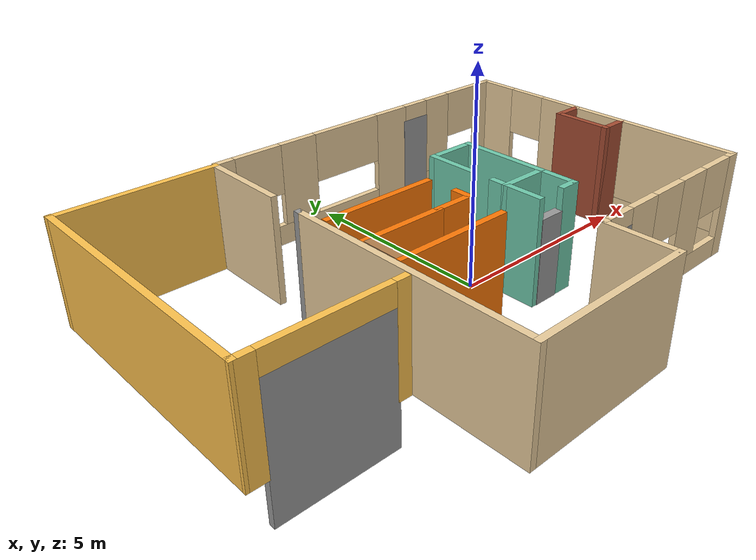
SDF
<?xml version='1.0'?>
<sdf version='1.6'>
  <model name='my_world'>
    <link name='Door_2'>
      <pose frame=''>0.765403 -1.37888 0 0 -0 0</pose>
      <self_collide>0</self_collide>
      <kinematic>0</kinematic>
      <visual name='Door_2_Visual'>
        <pose frame=''>0 0 1 0 -0 0</pose>
        <geometry>
          <box>
            <size>0.626242 0.2 2</size>
          </box>
        </geometry>
        <material>
          <script>
            <uri>file://media/materials/scripts/gazebo.material</uri>
            <name>Gazebo/Grey</name>
          </script>
          <ambient>0.3 0.3 0.3 1</ambient>
          <diffuse>0.7 0.7 0.7 1</diffuse>
          <specular>0.01 0.01 0.01 1</specular>
          <emissive>0 0 0 1</emissive>
          <shader type='pixel'/>
        </material>
        <transparency>0</transparency>
        <cast_shadows>1</cast_shadows>
      </visual>
      <collision name='Door_2_Collision'>
        <laser_retro>0</laser_retro>
        <max_contacts>10</max_contacts>
        <pose frame=''>0 0 1 0 -0 0</pose>
        <geometry>
          <box>
            <size>0.626242 0.2 2</size>
          </box>
        </geometry>
        <surface>
          <friction>
            <ode>
              <mu>1</mu>
              <mu2>1</mu2>
              <fdir1>0 0 0</fdir1>
              <slip1>0</slip1>
              <slip2>0</slip2>
            </ode>
            <torsional>
              <coefficient>1</coefficient>
              <patch_radius>0</patch_radius>
              <surface_radius>0</surface_radius>
              <use_patch_radius>1</use_patch_radius>
              <ode>
                <slip>0</slip>
              </ode>
            </torsional>
          </friction>
          <bounce>
            <restitution_coefficient>0</restitution_coefficient>
            <threshold>1e+06</threshold>
          </bounce>
          <contact>
            <collide_without_contact>0</collide_without_contact>
            <collide_without_contact_bitmask>1</collide_without_contact_bitmask>
            <collide_bitmask>1</collide_bitmask>
            <ode>
              <soft_cfm>0</soft_cfm>
              <soft_erp>0.2</soft_erp>
              <kp>1e+13</kp>
              <kd>1</kd>
              <max_vel>0.01</max_vel>
              <min_depth>0</min_depth>
            </ode>
            <bullet>
              <split_impulse>1</split_impulse>
              <split_impulse_penetration_threshold>-0.01</split_impulse_penetration_threshold>
              <soft_cfm>0</soft_cfm>
              <soft_erp>0.2</soft_erp>
              <kp>1e+13</kp>
              <kd>1</kd>
            </bullet>
          </contact>
        </surface>
      </collision>
    </link>
    <link name='Stairs_3'>
      <pose frame=''>0 0 0 0 -0 0</pose>
      <self_collide>0</self_collide>
      <kinematic>0</kinematic>
      <visual name='Stairs_3_Visual_0'>
        <pose frame=''>-0.655687 -0.838968 0.083333 0 0 -1.5708</pose>
        <geometry>
          <box>
            <size>0.863121 0.182638 0.166667</size>
          </box>
        </geometry>
        <material>
          <script>
            <uri>file://media/materials/scripts/gazebo.material</uri>
            <name>Gazebo/Wood</name>
          </script>
          <ambient>1 1 1 1</ambient>
          <diffuse>1 1 1 1</diffuse>
          <specular>0.2 0.2 0.2 1</specular>
          <emissive>0 0 0 1</emissive>
          <shader type='pixel'/>
        </material>
        <meta>
          <layer>0</layer>
        </meta>
        <transparency>0</transparency>
        <cast_shadows>1</cast_shadows>
      </visual>
      <visual name='Stairs_3_Visual_1'>
        <pose frame=''>-0.838325 -0.838968 0.25 0 0 -1.5708</pose>
        <geometry>
          <box>
            <size>0.863121 0.182638 0.166667</size>
          </box>
        </geometry>
        <material>
          <script>
            <uri>file://media/materials/scripts/gazebo.material</uri>
            <name>Gazebo/Wood</name>
          </script>
          <ambient>1 1 1 1</ambient>
          <diffuse>1 1 1 1</diffuse>
          <specular>0.2 0.2 0.2 1</specular>
          <emissive>0 0 0 1</emissive>
          <shader type='pixel'/>
        </material>
        <meta>
          <layer>0</layer>
        </meta>
        <transparency>0</transparency>
        <cast_shadows>1</cast_shadows>
      </visual>
      <visual name='Stairs_3_Visual_2'>
        <pose frame=''>-1.02096 -0.838968 0.416667 0 0 -1.5708</pose>
        <geometry>
          <box>
            <size>0.863121 0.182638 0.166667</size>
          </box>
        </geometry>
        <material>
          <script>
            <uri>file://media/materials/scripts/gazebo.material</uri>
            <name>Gazebo/Wood</name>
          </script>
          <ambient>1 1 1 1</ambient>
          <diffuse>1 1 1 1</diffuse>
          <specular>0.2 0.2 0.2 1</specular>
          <emissive>0 0 0 1</emissive>
          <shader type='pixel'/>
        </material>
        <meta>
          <layer>0</layer>
        </meta>
        <transparency>0</transparency>
        <cast_shadows>1</cast_shadows>
      </visual>
      <visual name='Stairs_3_Visual_8'>
        <pose frame=''>-2.11679 -0.838967 1.41667 0 0 -1.5708</pose>
        <geometry>
          <box>
            <size>0.863121 0.182638 0.166667</size>
          </box>
        </geometry>
        <material>
          <script>
            <uri>file://media/materials/scripts/gazebo.material</uri>
            <name>Gazebo/Wood</name>
          </script>
          <ambient>1 1 1 1</ambient>
          <diffuse>1 1 1 1</diffuse>
          <specular>0.2 0.2 0.2 1</specular>
          <emissive>0 0 0 1</emissive>
          <shader type='pixel'/>
        </material>
        <meta>
          <layer>0</layer>
        </meta>
        <transparency>0</transparency>
        <cast_shadows>1</cast_shadows>
      </visual>
      <visual name='Stairs_3_Visual_3'>
        <pose frame=''>-1.2036 -0.838968 0.583333 0 0 -1.5708</pose>
        <geometry>
          <box>
            <size>0.863121 0.182638 0.166667</size>
          </box>
        </geometry>
        <material>
          <script>
            <uri>file://media/materials/scripts/gazebo.material</uri>
            <name>Gazebo/Wood</name>
          </script>
          <ambient>1 1 1 1</ambient>
          <diffuse>1 1 1 1</diffuse>
          <specular>0.2 0.2 0.2 1</specular>
          <emissive>0 0 0 1</emissive>
          <shader type='pixel'/>
        </material>
        <meta>
          <layer>0</layer>
        </meta>
        <transparency>0</transparency>
        <cast_shadows>1</cast_shadows>
      </visual>
      <visual name='Stairs_3_Visual_4'>
        <pose frame=''>-1.38624 -0.838968 0.75 0 0 -1.5708</pose>
        <geometry>
          <box>
            <size>0.863121 0.182638 0.166667</size>
          </box>
        </geometry>
        <material>
          <script>
            <uri>file://media/materials/scripts/gazebo.material</uri>
            <name>Gazebo/Wood</name>
          </script>
          <ambient>1 1 1 1</ambient>
          <diffuse>1 1 1 1</diffuse>
          <specular>0.2 0.2 0.2 1</specular>
          <emissive>0 0 0 1</emissive>
          <shader type='pixel'/>
        </material>
        <meta>
          <layer>0</layer>
        </meta>
        <transparency>0</transparency>
        <cast_shadows>1</cast_shadows>
      </visual>
      <visual name='Stairs_3_Visual_5'>
        <pose frame=''>-1.56888 -0.838968 0.916667 0 0 -1.5708</pose>
        <geometry>
          <box>
            <size>0.863121 0.182638 0.166667</size>
          </box>
        </geometry>
        <material>
          <script>
            <uri>file://media/materials/scripts/gazebo.material</uri>
            <name>Gazebo/Wood</name>
          </script>
          <ambient>1 1 1 1</ambient>
          <diffuse>1 1 1 1</diffuse>
          <specular>0.2 0.2 0.2 1</specular>
          <emissive>0 0 0 1</emissive>
          <shader type='pixel'/>
        </material>
        <meta>
          <layer>0</layer>
        </meta>
        <transparency>0</transparency>
        <cast_shadows>1</cast_shadows>
      </visual>
      <visual name='Stairs_3_Visual_6'>
        <pose frame=''>-1.75151 -0.838968 1.08333 0 0 -1.5708</pose>
        <geometry>
          <box>
            <size>0.863121 0.182638 0.166667</size>
          </box>
        </geometry>
        <material>
          <script>
            <uri>file://media/materials/scripts/gazebo.material</uri>
            <name>Gazebo/Wood</name>
          </script>
          <ambient>1 1 1 1</ambient>
          <diffuse>1 1 1 1</diffuse>
          <specular>0.2 0.2 0.2 1</specular>
          <emissive>0 0 0 1</emissive>
          <shader type='pixel'/>
        </material>
        <meta>
          <layer>0</layer>
        </meta>
        <transparency>0</transparency>
        <cast_shadows>1</cast_shadows>
      </visual>
      <visual name='Stairs_3_Visual_7'>
        <pose frame=''>-1.93415 -0.838968 1.25 0 0 -1.5708</pose>
        <geometry>
          <box>
            <size>0.863121 0.182638 0.166667</size>
          </box>
        </geometry>
        <material>
          <script>
            <uri>file://media/materials/scripts/gazebo.material</uri>
            <name>Gazebo/Wood</name>
          </script>
          <ambient>1 1 1 1</ambient>
          <diffuse>1 1 1 1</diffuse>
          <specular>0.2 0.2 0.2 1</specular>
          <emissive>0 0 0 1</emissive>
          <shader type='pixel'/>
        </material>
        <meta>
          <layer>0</layer>
        </meta>
        <transparency>0</transparency>
        <cast_shadows>1</cast_shadows>
      </visual>
      <visual name='Stairs_3_Visual_9'>
        <pose frame=''>-2.29942 -0.838967 1.58333 0 0 -1.5708</pose>
        <geometry>
          <box>
            <size>0.863121 0.182638 0.166667</size>
          </box>
        </geometry>
        <material>
          <script>
            <uri>file://media/materials/scripts/gazebo.material</uri>
            <name>Gazebo/Wood</name>
          </script>
          <ambient>1 1 1 1</ambient>
          <diffuse>1 1 1 1</diffuse>
          <specular>0.2 0.2 0.2 1</specular>
          <emissive>0 0 0 1</emissive>
          <shader type='pixel'/>
        </material>
        <meta>
          <layer>0</layer>
        </meta>
        <transparency>0</transparency>
        <cast_shadows>1</cast_shadows>
      </visual>
      <visual name='Stairs_3_Visual_10'>
        <pose frame=''>-2.48206 -0.838967 1.75 0 0 -1.5708</pose>
        <geometry>
          <box>
            <size>0.863121 0.182638 0.166667</size>
          </box>
        </geometry>
        <material>
          <script>
            <uri>file://media/materials/scripts/gazebo.material</uri>
            <name>Gazebo/Wood</name>
          </script>
          <ambient>1 1 1 1</ambient>
          <diffuse>1 1 1 1</diffuse>
          <specular>0.2 0.2 0.2 1</specular>
          <emissive>0 0 0 1</emissive>
          <shader type='pixel'/>
        </material>
        <meta>
          <layer>0</layer>
        </meta>
        <transparency>0</transparency>
        <cast_shadows>1</cast_shadows>
      </visual>
      <visual name='Stairs_3_Visual_11'>
        <pose frame=''>-2.6647 -0.838967 1.91667 0 0 -1.5708</pose>
        <geometry>
          <box>
            <size>0.863121 0.182638 0.166667</size>
          </box>
        </geometry>
        <material>
          <script>
            <uri>file://media/materials/scripts/gazebo.material</uri>
            <name>Gazebo/Wood</name>
          </script>
          <ambient>1 1 1 1</ambient>
          <diffuse>1 1 1 1</diffuse>
          <specular>0.2 0.2 0.2 1</specular>
          <emissive>0 0 0 1</emissive>
          <shader type='pixel'/>
        </material>
        <meta>
          <layer>0</layer>
        </meta>
        <transparency>0</transparency>
        <cast_shadows>1</cast_shadows>
      </visual>
      <visual name='Stairs_3_Visual_12'>
        <pose frame=''>-2.84734 -0.838967 2.08333 0 0 -1.5708</pose>
        <geometry>
          <box>
            <size>0.863121 0.182638 0.166667</size>
          </box>
        </geometry>
        <material>
          <script>
            <uri>file://media/materials/scripts/gazebo.material</uri>
            <name>Gazebo/Wood</name>
          </script>
          <ambient>1 1 1 1</ambient>
          <diffuse>1 1 1 1</diffuse>
          <specular>0.2 0.2 0.2 1</specular>
          <emissive>0 0 0 1</emissive>
          <shader type='pixel'/>
        </material>
        <meta>
          <layer>0</layer>
        </meta>
        <transparency>0</transparency>
        <cast_shadows>1</cast_shadows>
      </visual>
      <visual name='Stairs_3_Visual_13'>
        <pose frame=''>-3.02997 -0.838967 2.25 0 0 -1.5708</pose>
        <geometry>
          <box>
            <size>0.863121 0.182638 0.166667</size>
          </box>
        </geometry>
        <material>
          <script>
            <uri>file://media/materials/scripts/gazebo.material</uri>
            <name>Gazebo/Wood</name>
          </script>
          <ambient>1 1 1 1</ambient>
          <diffuse>1 1 1 1</diffuse>
          <specular>0.2 0.2 0.2 1</specular>
          <emissive>0 0 0 1</emissive>
          <shader type='pixel'/>
        </material>
        <meta>
          <layer>0</layer>
        </meta>
        <transparency>0</transparency>
        <cast_shadows>1</cast_shadows>
      </visual>
      <visual name='Stairs_3_Visual_14'>
        <pose frame=''>-3.21261 -0.838967 2.41667 0 0 -1.5708</pose>
        <geometry>
          <box>
            <size>0.863121 0.182638 0.166667</size>
          </box>
        </geometry>
        <material>
          <script>
            <uri>file://media/materials/scripts/gazebo.material</uri>
            <name>Gazebo/Wood</name>
          </script>
          <ambient>1 1 1 1</ambient>
          <diffuse>1 1 1 1</diffuse>
          <specular>0.2 0.2 0.2 1</specular>
          <emissive>0 0 0 1</emissive>
          <shader type='pixel'/>
        </material>
        <meta>
          <layer>0</layer>
        </meta>
        <transparency>0</transparency>
        <cast_shadows>1</cast_shadows>
      </visual>
      <collision name='Stairs_3_Collision_13'>
        <laser_retro>0</laser_retro>
        <max_contacts>10</max_contacts>
        <pose frame=''>-3.02997 -0.838967 2.25 0 0 -1.5708</pose>
        <geometry>
          <box>
            <size>0.863121 0.182638 0.166667</size>
          </box>
        </geometry>
        <surface>
          <friction>
            <ode>
              <mu>1</mu>
              <mu2>1</mu2>
              <fdir1>0 0 0</fdir1>
              <slip1>0</slip1>
              <slip2>0</slip2>
            </ode>
            <torsional>
              <coefficient>1</coefficient>
              <patch_radius>0</patch_radius>
              <surface_radius>0</surface_radius>
              <use_patch_radius>1</use_patch_radius>
              <ode>
                <slip>0</slip>
              </ode>
            </torsional>
          </friction>
          <bounce>
            <restitution_coefficient>0</restitution_coefficient>
            <threshold>1e+06</threshold>
          </bounce>
          <contact>
            <collide_without_contact>0</collide_without_contact>
            <collide_without_contact_bitmask>1</collide_without_contact_bitmask>
            <collide_bitmask>1</collide_bitmask>
            <ode>
              <soft_cfm>0</soft_cfm>
              <soft_erp>0.2</soft_erp>
              <kp>1e+13</kp>
              <kd>1</kd>
              <max_vel>0.01</max_vel>
              <min_depth>0</min_depth>
            </ode>
            <bullet>
              <split_impulse>1</split_impulse>
              <split_impulse_penetration_threshold>-0.01</split_impulse_penetration_threshold>
              <soft_cfm>0</soft_cfm>
              <soft_erp>0.2</soft_erp>
              <kp>1e+13</kp>
              <kd>1</kd>
            </bullet>
          </contact>
        </surface>
      </collision>
      <collision name='Stairs_3_Collision_2'>
        <laser_retro>0</laser_retro>
        <max_contacts>10</max_contacts>
        <pose frame=''>-1.02096 -0.838968 0.416667 0 0 -1.5708</pose>
        <geometry>
          <box>
            <size>0.863121 0.182638 0.166667</size>
          </box>
        </geometry>
        <surface>
          <friction>
            <ode>
              <mu>1</mu>
              <mu2>1</mu2>
              <fdir1>0 0 0</fdir1>
              <slip1>0</slip1>
              <slip2>0</slip2>
            </ode>
            <torsional>
              <coefficient>1</coefficient>
              <patch_radius>0</patch_radius>
              <surface_radius>0</surface_radius>
              <use_patch_radius>1</use_patch_radius>
              <ode>
                <slip>0</slip>
              </ode>
            </torsional>
          </friction>
          <bounce>
            <restitution_coefficient>0</restitution_coefficient>
            <threshold>1e+06</threshold>
          </bounce>
          <contact>
            <collide_without_contact>0</collide_without_contact>
            <collide_without_contact_bitmask>1</collide_without_contact_bitmask>
            <collide_bitmask>1</collide_bitmask>
            <ode>
              <soft_cfm>0</soft_cfm>
              <soft_erp>0.2</soft_erp>
              <kp>1e+13</kp>
              <kd>1</kd>
              <max_vel>0.01</max_vel>
              <min_depth>0</min_depth>
            </ode>
            <bullet>
              <split_impulse>1</split_impulse>
              <split_impulse_penetration_threshold>-0.01</split_impulse_penetration_threshold>
              <soft_cfm>0</soft_cfm>
              <soft_erp>0.2</soft_erp>
              <kp>1e+13</kp>
              <kd>1</kd>
            </bullet>
          </contact>
        </surface>
      </collision>
      <collision name='Stairs_3_Collision_0'>
        <laser_retro>0</laser_retro>
        <max_contacts>10</max_contacts>
        <pose frame=''>-0.655687 -0.838968 0.083333 0 0 -1.5708</pose>
        <geometry>
          <box>
            <size>0.863121 0.182638 0.166667</size>
          </box>
        </geometry>
        <surface>
          <friction>
            <ode>
              <mu>1</mu>
              <mu2>1</mu2>
              <fdir1>0 0 0</fdir1>
              <slip1>0</slip1>
              <slip2>0</slip2>
            </ode>
            <torsional>
              <coefficient>1</coefficient>
              <patch_radius>0</patch_radius>
              <surface_radius>0</surface_radius>
              <use_patch_radius>1</use_patch_radius>
              <ode>
                <slip>0</slip>
              </ode>
            </torsional>
          </friction>
          <bounce>
            <restitution_coefficient>0</restitution_coefficient>
            <threshold>1e+06</threshold>
          </bounce>
          <contact>
            <collide_without_contact>0</collide_without_contact>
            <collide_without_contact_bitmask>1</collide_without_contact_bitmask>
            <collide_bitmask>1</collide_bitmask>
            <ode>
              <soft_cfm>0</soft_cfm>
              <soft_erp>0.2</soft_erp>
              <kp>1e+13</kp>
              <kd>1</kd>
              <max_vel>0.01</max_vel>
              <min_depth>0</min_depth>
            </ode>
            <bullet>
              <split_impulse>1</split_impulse>
              <split_impulse_penetration_threshold>-0.01</split_impulse_penetration_threshold>
              <soft_cfm>0</soft_cfm>
              <soft_erp>0.2</soft_erp>
              <kp>1e+13</kp>
              <kd>1</kd>
            </bullet>
          </contact>
        </surface>
      </collision>
      <collision name='Stairs_3_Collision_1'>
        <laser_retro>0</laser_retro>
        <max_contacts>10</max_contacts>
        <pose frame=''>-0.838325 -0.838968 0.25 0 0 -1.5708</pose>
        <geometry>
          <box>
            <size>0.863121 0.182638 0.166667</size>
          </box>
        </geometry>
        <surface>
          <friction>
            <ode>
              <mu>1</mu>
              <mu2>1</mu2>
              <fdir1>0 0 0</fdir1>
              <slip1>0</slip1>
              <slip2>0</slip2>
            </ode>
            <torsional>
              <coefficient>1</coefficient>
              <patch_radius>0</patch_radius>
              <surface_radius>0</surface_radius>
              <use_patch_radius>1</use_patch_radius>
              <ode>
                <slip>0</slip>
              </ode>
            </torsional>
          </friction>
          <bounce>
            <restitution_coefficient>0</restitution_coefficient>
            <threshold>1e+06</threshold>
          </bounce>
          <contact>
            <collide_without_contact>0</collide_without_contact>
            <collide_without_contact_bitmask>1</collide_without_contact_bitmask>
            <collide_bitmask>1</collide_bitmask>
            <ode>
              <soft_cfm>0</soft_cfm>
              <soft_erp>0.2</soft_erp>
              <kp>1e+13</kp>
              <kd>1</kd>
              <max_vel>0.01</max_vel>
              <min_depth>0</min_depth>
            </ode>
            <bullet>
              <split_impulse>1</split_impulse>
              <split_impulse_penetration_threshold>-0.01</split_impulse_penetration_threshold>
              <soft_cfm>0</soft_cfm>
              <soft_erp>0.2</soft_erp>
              <kp>1e+13</kp>
              <kd>1</kd>
            </bullet>
          </contact>
        </surface>
      </collision>
      <collision name='Stairs_3_Collision_3'>
        <laser_retro>0</laser_retro>
        <max_contacts>10</max_contacts>
        <pose frame=''>-1.2036 -0.838968 0.583333 0 0 -1.5708</pose>
        <geometry>
          <box>
            <size>0.863121 0.182638 0.166667</size>
          </box>
        </geometry>
        <surface>
          <friction>
            <ode>
              <mu>1</mu>
              <mu2>1</mu2>
              <fdir1>0 0 0</fdir1>
              <slip1>0</slip1>
              <slip2>0</slip2>
            </ode>
            <torsional>
              <coefficient>1</coefficient>
              <patch_radius>0</patch_radius>
              <surface_radius>0</surface_radius>
              <use_patch_radius>1</use_patch_radius>
              <ode>
                <slip>0</slip>
              </ode>
            </torsional>
          </friction>
          <bounce>
            <restitution_coefficient>0</restitution_coefficient>
            <threshold>1e+06</threshold>
          </bounce>
          <contact>
            <collide_without_contact>0</collide_without_contact>
            <collide_without_contact_bitmask>1</collide_without_contact_bitmask>
            <collide_bitmask>1</collide_bitmask>
            <ode>
              <soft_cfm>0</soft_cfm>
              <soft_erp>0.2</soft_erp>
              <kp>1e+13</kp>
              <kd>1</kd>
              <max_vel>0.01</max_vel>
              <min_depth>0</min_depth>
            </ode>
            <bullet>
              <split_impulse>1</split_impulse>
              <split_impulse_penetration_threshold>-0.01</split_impulse_penetration_threshold>
              <soft_cfm>0</soft_cfm>
              <soft_erp>0.2</soft_erp>
              <kp>1e+13</kp>
              <kd>1</kd>
            </bullet>
          </contact>
        </surface>
      </collision>
      <collision name='Stairs_3_Collision_4'>
        <laser_retro>0</laser_retro>
        <max_contacts>10</max_contacts>
        <pose frame=''>-1.38624 -0.838968 0.75 0 0 -1.5708</pose>
        <geometry>
          <box>
            <size>0.863121 0.182638 0.166667</size>
          </box>
        </geometry>
        <surface>
          <friction>
            <ode>
              <mu>1</mu>
              <mu2>1</mu2>
              <fdir1>0 0 0</fdir1>
              <slip1>0</slip1>
              <slip2>0</slip2>
            </ode>
            <torsional>
              <coefficient>1</coefficient>
              <patch_radius>0</patch_radius>
              <surface_radius>0</surface_radius>
              <use_patch_radius>1</use_patch_radius>
              <ode>
                <slip>0</slip>
              </ode>
            </torsional>
          </friction>
          <bounce>
            <restitution_coefficient>0</restitution_coefficient>
            <threshold>1e+06</threshold>
          </bounce>
          <contact>
            <collide_without_contact>0</collide_without_contact>
            <collide_without_contact_bitmask>1</collide_without_contact_bitmask>
            <collide_bitmask>1</collide_bitmask>
            <ode>
              <soft_cfm>0</soft_cfm>
              <soft_erp>0.2</soft_erp>
              <kp>1e+13</kp>
              <kd>1</kd>
              <max_vel>0.01</max_vel>
              <min_depth>0</min_depth>
            </ode>
            <bullet>
              <split_impulse>1</split_impulse>
              <split_impulse_penetration_threshold>-0.01</split_impulse_penetration_threshold>
              <soft_cfm>0</soft_cfm>
              <soft_erp>0.2</soft_erp>
              <kp>1e+13</kp>
              <kd>1</kd>
            </bullet>
          </contact>
        </surface>
      </collision>
      <collision name='Stairs_3_Collision_5'>
        <laser_retro>0</laser_retro>
        <max_contacts>10</max_contacts>
        <pose frame=''>-1.56888 -0.838968 0.916667 0 0 -1.5708</pose>
        <geometry>
          <box>
            <size>0.863121 0.182638 0.166667</size>
          </box>
        </geometry>
        <surface>
          <friction>
            <ode>
              <mu>1</mu>
              <mu2>1</mu2>
              <fdir1>0 0 0</fdir1>
              <slip1>0</slip1>
              <slip2>0</slip2>
            </ode>
            <torsional>
              <coefficient>1</coefficient>
              <patch_radius>0</patch_radius>
              <surface_radius>0</surface_radius>
              <use_patch_radius>1</use_patch_radius>
              <ode>
                <slip>0</slip>
              </ode>
            </torsional>
          </friction>
          <bounce>
            <restitution_coefficient>0</restitution_coefficient>
            <threshold>1e+06</threshold>
          </bounce>
          <contact>
            <collide_without_contact>0</collide_without_contact>
            <collide_without_contact_bitmask>1</collide_without_contact_bitmask>
            <collide_bitmask>1</collide_bitmask>
            <ode>
              <soft_cfm>0</soft_cfm>
              <soft_erp>0.2</soft_erp>
              <kp>1e+13</kp>
              <kd>1</kd>
              <max_vel>0.01</max_vel>
              <min_depth>0</min_depth>
            </ode>
            <bullet>
              <split_impulse>1</split_impulse>
              <split_impulse_penetration_threshold>-0.01</split_impulse_penetration_threshold>
              <soft_cfm>0</soft_cfm>
              <soft_erp>0.2</soft_erp>
              <kp>1e+13</kp>
              <kd>1</kd>
            </bullet>
          </contact>
        </surface>
      </collision>
      <collision name='Stairs_3_Collision_7'>
        <laser_retro>0</laser_retro>
        <max_contacts>10</max_contacts>
        <pose frame=''>-1.93415 -0.838968 1.25 0 0 -1.5708</pose>
        <geometry>
          <box>
            <size>0.863121 0.182638 0.166667</size>
          </box>
        </geometry>
        <surface>
          <friction>
            <ode>
              <mu>1</mu>
              <mu2>1</mu2>
              <fdir1>0 0 0</fdir1>
              <slip1>0</slip1>
              <slip2>0</slip2>
            </ode>
            <torsional>
              <coefficient>1</coefficient>
              <patch_radius>0</patch_radius>
              <surface_radius>0</surface_radius>
              <use_patch_radius>1</use_patch_radius>
              <ode>
                <slip>0</slip>
              </ode>
            </torsional>
          </friction>
          <bounce>
            <restitution_coefficient>0</restitution_coefficient>
            <threshold>1e+06</threshold>
          </bounce>
          <contact>
            <collide_without_contact>0</collide_without_contact>
            <collide_without_contact_bitmask>1</collide_without_contact_bitmask>
            <collide_bitmask>1</collide_bitmask>
            <ode>
              <soft_cfm>0</soft_cfm>
              <soft_erp>0.2</soft_erp>
              <kp>1e+13</kp>
              <kd>1</kd>
              <max_vel>0.01</max_vel>
              <min_depth>0</min_depth>
            </ode>
            <bullet>
              <split_impulse>1</split_impulse>
              <split_impulse_penetration_threshold>-0.01</split_impulse_penetration_threshold>
              <soft_cfm>0</soft_cfm>
              <soft_erp>0.2</soft_erp>
              <kp>1e+13</kp>
              <kd>1</kd>
            </bullet>
          </contact>
        </surface>
      </collision>
      <collision name='Stairs_3_Collision_6'>
        <laser_retro>0</laser_retro>
        <max_contacts>10</max_contacts>
        <pose frame=''>-1.75151 -0.838968 1.08333 0 0 -1.5708</pose>
        <geometry>
          <box>
            <size>0.863121 0.182638 0.166667</size>
          </box>
        </geometry>
        <surface>
          <friction>
            <ode>
              <mu>1</mu>
              <mu2>1</mu2>
              <fdir1>0 0 0</fdir1>
              <slip1>0</slip1>
              <slip2>0</slip2>
            </ode>
            <torsional>
              <coefficient>1</coefficient>
              <patch_radius>0</patch_radius>
              <surface_radius>0</surface_radius>
              <use_patch_radius>1</use_patch_radius>
              <ode>
                <slip>0</slip>
              </ode>
            </torsional>
          </friction>
          <bounce>
            <restitution_coefficient>0</restitution_coefficient>
            <threshold>1e+06</threshold>
          </bounce>
          <contact>
            <collide_without_contact>0</collide_without_contact>
            <collide_without_contact_bitmask>1</collide_without_contact_bitmask>
            <collide_bitmask>1</collide_bitmask>
            <ode>
              <soft_cfm>0</soft_cfm>
              <soft_erp>0.2</soft_erp>
              <kp>1e+13</kp>
              <kd>1</kd>
              <max_vel>0.01</max_vel>
              <min_depth>0</min_depth>
            </ode>
            <bullet>
              <split_impulse>1</split_impulse>
              <split_impulse_penetration_threshold>-0.01</split_impulse_penetration_threshold>
              <soft_cfm>0</soft_cfm>
              <soft_erp>0.2</soft_erp>
              <kp>1e+13</kp>
              <kd>1</kd>
            </bullet>
          </contact>
        </surface>
      </collision>
      <collision name='Stairs_3_Collision_8'>
        <laser_retro>0</laser_retro>
        <max_contacts>10</max_contacts>
        <pose frame=''>-2.11679 -0.838967 1.41667 0 0 -1.5708</pose>
        <geometry>
          <box>
            <size>0.863121 0.182638 0.166667</size>
          </box>
        </geometry>
        <surface>
          <friction>
            <ode>
              <mu>1</mu>
              <mu2>1</mu2>
              <fdir1>0 0 0</fdir1>
              <slip1>0</slip1>
              <slip2>0</slip2>
            </ode>
            <torsional>
              <coefficient>1</coefficient>
              <patch_radius>0</patch_radius>
              <surface_radius>0</surface_radius>
              <use_patch_radius>1</use_patch_radius>
              <ode>
                <slip>0</slip>
              </ode>
            </torsional>
          </friction>
          <bounce>
            <restitution_coefficient>0</restitution_coefficient>
            <threshold>1e+06</threshold>
          </bounce>
          <contact>
            <collide_without_contact>0</collide_without_contact>
            <collide_without_contact_bitmask>1</collide_without_contact_bitmask>
            <collide_bitmask>1</collide_bitmask>
            <ode>
              <soft_cfm>0</soft_cfm>
              <soft_erp>0.2</soft_erp>
              <kp>1e+13</kp>
              <kd>1</kd>
              <max_vel>0.01</max_vel>
              <min_depth>0</min_depth>
            </ode>
            <bullet>
              <split_impulse>1</split_impulse>
              <split_impulse_penetration_threshold>-0.01</split_impulse_penetration_threshold>
              <soft_cfm>0</soft_cfm>
              <soft_erp>0.2</soft_erp>
              <kp>1e+13</kp>
              <kd>1</kd>
            </bullet>
          </contact>
        </surface>
      </collision>
      <collision name='Stairs_3_Collision_9'>
        <laser_retro>0</laser_retro>
        <max_contacts>10</max_contacts>
        <pose frame=''>-2.29942 -0.838967 1.58333 0 0 -1.5708</pose>
        <geometry>
          <box>
            <size>0.863121 0.182638 0.166667</size>
          </box>
        </geometry>
        <surface>
          <friction>
            <ode>
              <mu>1</mu>
              <mu2>1</mu2>
              <fdir1>0 0 0</fdir1>
              <slip1>0</slip1>
              <slip2>0</slip2>
            </ode>
            <torsional>
              <coefficient>1</coefficient>
              <patch_radius>0</patch_radius>
              <surface_radius>0</surface_radius>
              <use_patch_radius>1</use_patch_radius>
              <ode>
                <slip>0</slip>
              </ode>
            </torsional>
          </friction>
          <bounce>
            <restitution_coefficient>0</restitution_coefficient>
            <threshold>1e+06</threshold>
          </bounce>
          <contact>
            <collide_without_contact>0</collide_without_contact>
            <collide_without_contact_bitmask>1</collide_without_contact_bitmask>
            <collide_bitmask>1</collide_bitmask>
            <ode>
              <soft_cfm>0</soft_cfm>
              <soft_erp>0.2</soft_erp>
              <kp>1e+13</kp>
              <kd>1</kd>
              <max_vel>0.01</max_vel>
              <min_depth>0</min_depth>
            </ode>
            <bullet>
              <split_impulse>1</split_impulse>
              <split_impulse_penetration_threshold>-0.01</split_impulse_penetration_threshold>
              <soft_cfm>0</soft_cfm>
              <soft_erp>0.2</soft_erp>
              <kp>1e+13</kp>
              <kd>1</kd>
            </bullet>
          </contact>
        </surface>
      </collision>
      <collision name='Stairs_3_Collision_11'>
        <laser_retro>0</laser_retro>
        <max_contacts>10</max_contacts>
        <pose frame=''>-2.6647 -0.838967 1.91667 0 0 -1.5708</pose>
        <geometry>
          <box>
            <size>0.863121 0.182638 0.166667</size>
          </box>
        </geometry>
        <surface>
          <friction>
            <ode>
              <mu>1</mu>
              <mu2>1</mu2>
              <fdir1>0 0 0</fdir1>
              <slip1>0</slip1>
              <slip2>0</slip2>
            </ode>
            <torsional>
              <coefficient>1</coefficient>
              <patch_radius>0</patch_radius>
              <surface_radius>0</surface_radius>
              <use_patch_radius>1</use_patch_radius>
              <ode>
                <slip>0</slip>
              </ode>
            </torsional>
          </friction>
          <bounce>
            <restitution_coefficient>0</restitution_coefficient>
            <threshold>1e+06</threshold>
          </bounce>
          <contact>
            <collide_without_contact>0</collide_without_contact>
            <collide_without_contact_bitmask>1</collide_without_contact_bitmask>
            <collide_bitmask>1</collide_bitmask>
            <ode>
              <soft_cfm>0</soft_cfm>
              <soft_erp>0.2</soft_erp>
              <kp>1e+13</kp>
              <kd>1</kd>
              <max_vel>0.01</max_vel>
              <min_depth>0</min_depth>
            </ode>
            <bullet>
              <split_impulse>1</split_impulse>
              <split_impulse_penetration_threshold>-0.01</split_impulse_penetration_threshold>
              <soft_cfm>0</soft_cfm>
              <soft_erp>0.2</soft_erp>
              <kp>1e+13</kp>
              <kd>1</kd>
            </bullet>
          </contact>
        </surface>
      </collision>
      <collision name='Stairs_3_Collision_12'>
        <laser_retro>0</laser_retro>
        <max_contacts>10</max_contacts>
        <pose frame=''>-2.84734 -0.838967 2.08333 0 0 -1.5708</pose>
        <geometry>
          <box>
            <size>0.863121 0.182638 0.166667</size>
          </box>
        </geometry>
        <surface>
          <friction>
            <ode>
              <mu>1</mu>
              <mu2>1</mu2>
              <fdir1>0 0 0</fdir1>
              <slip1>0</slip1>
              <slip2>0</slip2>
            </ode>
            <torsional>
              <coefficient>1</coefficient>
              <patch_radius>0</patch_radius>
              <surface_radius>0</surface_radius>
              <use_patch_radius>1</use_patch_radius>
              <ode>
                <slip>0</slip>
              </ode>
            </torsional>
          </friction>
          <bounce>
            <restitution_coefficient>0</restitution_coefficient>
            <threshold>1e+06</threshold>
          </bounce>
          <contact>
            <collide_without_contact>0</collide_without_contact>
            <collide_without_contact_bitmask>1</collide_without_contact_bitmask>
            <collide_bitmask>1</collide_bitmask>
            <ode>
              <soft_cfm>0</soft_cfm>
              <soft_erp>0.2</soft_erp>
              <kp>1e+13</kp>
              <kd>1</kd>
              <max_vel>0.01</max_vel>
              <min_depth>0</min_depth>
            </ode>
            <bullet>
              <split_impulse>1</split_impulse>
              <split_impulse_penetration_threshold>-0.01</split_impulse_penetration_threshold>
              <soft_cfm>0</soft_cfm>
              <soft_erp>0.2</soft_erp>
              <kp>1e+13</kp>
              <kd>1</kd>
            </bullet>
          </contact>
        </surface>
      </collision>
      <collision name='Stairs_3_Collision_10'>
        <laser_retro>0</laser_retro>
        <max_contacts>10</max_contacts>
        <pose frame=''>-2.48206 -0.838967 1.75 0 0 -1.5708</pose>
        <geometry>
          <box>
            <size>0.863121 0.182638 0.166667</size>
          </box>
        </geometry>
        <surface>
          <friction>
            <ode>
              <mu>1</mu>
              <mu2>1</mu2>
              <fdir1>0 0 0</fdir1>
              <slip1>0</slip1>
              <slip2>0</slip2>
            </ode>
            <torsional>
              <coefficient>1</coefficient>
              <patch_radius>0</patch_radius>
              <surface_radius>0</surface_radius>
              <use_patch_radius>1</use_patch_radius>
              <ode>
                <slip>0</slip>
              </ode>
            </torsional>
          </friction>
          <bounce>
            <restitution_coefficient>0</restitution_coefficient>
            <threshold>1e+06</threshold>
          </bounce>
          <contact>
            <collide_without_contact>0</collide_without_contact>
            <collide_without_contact_bitmask>1</collide_without_contact_bitmask>
            <collide_bitmask>1</collide_bitmask>
            <ode>
              <soft_cfm>0</soft_cfm>
              <soft_erp>0.2</soft_erp>
              <kp>1e+13</kp>
              <kd>1</kd>
              <max_vel>0.01</max_vel>
              <min_depth>0</min_depth>
            </ode>
            <bullet>
              <split_impulse>1</split_impulse>
              <split_impulse_penetration_threshold>-0.01</split_impulse_penetration_threshold>
              <soft_cfm>0</soft_cfm>
              <soft_erp>0.2</soft_erp>
              <kp>1e+13</kp>
              <kd>1</kd>
            </bullet>
          </contact>
        </surface>
      </collision>
      <collision name='Stairs_3_Collision_14'>
        <laser_retro>0</laser_retro>
        <max_contacts>10</max_contacts>
        <pose frame=''>-3.21261 -0.838967 2.41667 0 0 -1.5708</pose>
        <geometry>
          <box>
            <size>0.863121 0.182638 0.166667</size>
          </box>
        </geometry>
        <surface>
          <friction>
            <ode>
              <mu>1</mu>
              <mu2>1</mu2>
              <fdir1>0 0 0</fdir1>
              <slip1>0</slip1>
              <slip2>0</slip2>
            </ode>
            <torsional>
              <coefficient>1</coefficient>
              <patch_radius>0</patch_radius>
              <surface_radius>0</surface_radius>
              <use_patch_radius>1</use_patch_radius>
              <ode>
                <slip>0</slip>
              </ode>
            </torsional>
          </friction>
          <bounce>
            <restitution_coefficient>0</restitution_coefficient>
            <threshold>1e+06</threshold>
          </bounce>
          <contact>
            <collide_without_contact>0</collide_without_contact>
            <collide_without_contact_bitmask>1</collide_without_contact_bitmask>
            <collide_bitmask>1</collide_bitmask>
            <ode>
              <soft_cfm>0</soft_cfm>
              <soft_erp>0.2</soft_erp>
              <kp>1e+13</kp>
              <kd>1</kd>
              <max_vel>0.01</max_vel>
              <min_depth>0</min_depth>
            </ode>
            <bullet>
              <split_impulse>1</split_impulse>
              <split_impulse_penetration_threshold>-0.01</split_impulse_penetration_threshold>
              <soft_cfm>0</soft_cfm>
              <soft_erp>0.2</soft_erp>
              <kp>1e+13</kp>
              <kd>1</kd>
            </bullet>
          </contact>
        </surface>
      </collision>
    </link>
    <link name='Wall_0'>
      <pose frame=''>5.30002 0.8 0 0 0 -1.5708</pose>
      <self_collide>0</self_collide>
      <kinematic>0</kinematic>
      <visual name='Wall_0_Visual_0'>
        <pose frame=''>-3.20604 0 1.25 0 -0 0</pose>
        <geometry>
          <box>
            <size>1.08792 0.15 2.5</size>
          </box>
        </geometry>
        <material>
          <script>
            <uri>file://media/materials/scripts/gazebo.material</uri>
            <name>Gazebo/Grey</name>
          </script>
          <ambient>0.921569 0.807843 0.615686 1</ambient>
          <diffuse>0.7 0.7 0.7 1</diffuse>
          <specular>0.01 0.01 0.01 1</specular>
          <emissive>0 0 0 1</emissive>
          <shader type='pixel'/>
        </material>
        <meta>
          <layer>0</layer>
        </meta>
        <transparency>0</transparency>
        <cast_shadows>1</cast_shadows>
      </visual>
      <visual name='Wall_0_Visual_1'>
        <pose frame=''>0.543962 0 0.25 0 -0 0</pose>
        <geometry>
          <box>
            <size>6.41208 0.15 0.5</size>
          </box>
        </geometry>
        <material>
          <script>
            <uri>file://media/materials/scripts/gazebo.material</uri>
            <name>Gazebo/Grey</name>
          </script>
          <ambient>0.921569 0.807843 0.615686 1</ambient>
          <diffuse>0.7 0.7 0.7 1</diffuse>
          <specular>0.01 0.01 0.01 1</specular>
          <emissive>0 0 0 1</emissive>
          <shader type='pixel'/>
        </material>
        <meta>
          <layer>0</layer>
        </meta>
        <transparency>0</transparency>
        <cast_shadows>1</cast_shadows>
      </visual>
      <visual name='Wall_0_Visual_2'>
        <pose frame=''>1.05042 0 1.5 0 -0 0</pose>
        <geometry>
          <box>
            <size>5.39915 0.15 2</size>
          </box>
        </geometry>
        <material>
          <script>
            <uri>file://media/materials/scripts/gazebo.material</uri>
            <name>Gazebo/Grey</name>
          </script>
          <ambient>0.921569 0.807843 0.615686 1</ambient>
          <diffuse>0.7 0.7 0.7 1</diffuse>
          <specular>0.01 0.01 0.01 1</specular>
          <emissive>0 0 0 1</emissive>
          <shader type='pixel'/>
        </material>
        <meta>
          <layer>0</layer>
        </meta>
        <transparency>0</transparency>
        <cast_shadows>1</cast_shadows>
      </visual>
      <visual name='Wall_0_Visual_3'>
        <pose frame=''>-2.15562 0 1.9 0 -0 0</pose>
        <geometry>
          <box>
            <size>1.01292 0.15 1.2</size>
          </box>
        </geometry>
        <material>
          <script>
            <uri>file://media/materials/scripts/gazebo.material</uri>
            <name>Gazebo/Grey</name>
          </script>
          <ambient>0.921569 0.807843 0.615686 1</ambient>
          <diffuse>0.7 0.7 0.7 1</diffuse>
          <specular>0.01 0.01 0.01 1</specular>
          <emissive>0 0 0 1</emissive>
          <shader type='pixel'/>
        </material>
        <meta>
          <layer>0</layer>
        </meta>
        <transparency>0</transparency>
        <cast_shadows>1</cast_shadows>
      </visual>
      <collision name='Wall_0_Collision_0'>
        <laser_retro>0</laser_retro>
        <max_contacts>10</max_contacts>
        <pose frame=''>-3.20604 0 1.25 0 -0 0</pose>
        <geometry>
          <box>
            <size>1.08792 0.15 2.5</size>
          </box>
        </geometry>
        <surface>
          <friction>
            <ode>
              <mu>1</mu>
              <mu2>1</mu2>
              <fdir1>0 0 0</fdir1>
              <slip1>0</slip1>
              <slip2>0</slip2>
            </ode>
            <torsional>
              <coefficient>1</coefficient>
              <patch_radius>0</patch_radius>
              <surface_radius>0</surface_radius>
              <use_patch_radius>1</use_patch_radius>
              <ode>
                <slip>0</slip>
              </ode>
            </torsional>
          </friction>
          <bounce>
            <restitution_coefficient>0</restitution_coefficient>
            <threshold>1e+06</threshold>
          </bounce>
          <contact>
            <collide_without_contact>0</collide_without_contact>
            <collide_without_contact_bitmask>1</collide_without_contact_bitmask>
            <collide_bitmask>1</collide_bitmask>
            <ode>
              <soft_cfm>0</soft_cfm>
              <soft_erp>0.2</soft_erp>
              <kp>1e+13</kp>
              <kd>1</kd>
              <max_vel>0.01</max_vel>
              <min_depth>0</min_depth>
            </ode>
            <bullet>
              <split_impulse>1</split_impulse>
              <split_impulse_penetration_threshold>-0.01</split_impulse_penetration_threshold>
              <soft_cfm>0</soft_cfm>
              <soft_erp>0.2</soft_erp>
              <kp>1e+13</kp>
              <kd>1</kd>
            </bullet>
          </contact>
        </surface>
      </collision>
      <collision name='Wall_0_Collision_3'>
        <laser_retro>0</laser_retro>
        <max_contacts>10</max_contacts>
        <pose frame=''>-2.15562 0 1.9 0 -0 0</pose>
        <geometry>
          <box>
            <size>1.01292 0.15 1.2</size>
          </box>
        </geometry>
        <surface>
          <friction>
            <ode>
              <mu>1</mu>
              <mu2>1</mu2>
              <fdir1>0 0 0</fdir1>
              <slip1>0</slip1>
              <slip2>0</slip2>
            </ode>
            <torsional>
              <coefficient>1</coefficient>
              <patch_radius>0</patch_radius>
              <surface_radius>0</surface_radius>
              <use_patch_radius>1</use_patch_radius>
              <ode>
                <slip>0</slip>
              </ode>
            </torsional>
          </friction>
          <bounce>
            <restitution_coefficient>0</restitution_coefficient>
            <threshold>1e+06</threshold>
          </bounce>
          <contact>
            <collide_without_contact>0</collide_without_contact>
            <collide_without_contact_bitmask>1</collide_without_contact_bitmask>
            <collide_bitmask>1</collide_bitmask>
            <ode>
              <soft_cfm>0</soft_cfm>
              <soft_erp>0.2</soft_erp>
              <kp>1e+13</kp>
              <kd>1</kd>
              <max_vel>0.01</max_vel>
              <min_depth>0</min_depth>
            </ode>
            <bullet>
              <split_impulse>1</split_impulse>
              <split_impulse_penetration_threshold>-0.01</split_impulse_penetration_threshold>
              <soft_cfm>0</soft_cfm>
              <soft_erp>0.2</soft_erp>
              <kp>1e+13</kp>
              <kd>1</kd>
            </bullet>
          </contact>
        </surface>
      </collision>
      <collision name='Wall_0_Collision_1'>
        <laser_retro>0</laser_retro>
        <max_contacts>10</max_contacts>
        <pose frame=''>0.543962 0 0.25 0 -0 0</pose>
        <geometry>
          <box>
            <size>6.41208 0.15 0.5</size>
          </box>
        </geometry>
        <surface>
          <friction>
            <ode>
              <mu>1</mu>
              <mu2>1</mu2>
              <fdir1>0 0 0</fdir1>
              <slip1>0</slip1>
              <slip2>0</slip2>
            </ode>
            <torsional>
              <coefficient>1</coefficient>
              <patch_radius>0</patch_radius>
              <surface_radius>0</surface_radius>
              <use_patch_radius>1</use_patch_radius>
              <ode>
                <slip>0</slip>
              </ode>
            </torsional>
          </friction>
          <bounce>
            <restitution_coefficient>0</restitution_coefficient>
            <threshold>1e+06</threshold>
          </bounce>
          <contact>
            <collide_without_contact>0</collide_without_contact>
            <collide_without_contact_bitmask>1</collide_without_contact_bitmask>
            <collide_bitmask>1</collide_bitmask>
            <ode>
              <soft_cfm>0</soft_cfm>
              <soft_erp>0.2</soft_erp>
              <kp>1e+13</kp>
              <kd>1</kd>
              <max_vel>0.01</max_vel>
              <min_depth>0</min_depth>
            </ode>
            <bullet>
              <split_impulse>1</split_impulse>
              <split_impulse_penetration_threshold>-0.01</split_impulse_penetration_threshold>
              <soft_cfm>0</soft_cfm>
              <soft_erp>0.2</soft_erp>
              <kp>1e+13</kp>
              <kd>1</kd>
            </bullet>
          </contact>
        </surface>
      </collision>
      <collision name='Wall_0_Collision_2'>
        <laser_retro>0</laser_retro>
        <max_contacts>10</max_contacts>
        <pose frame=''>1.05042 0 1.5 0 -0 0</pose>
        <geometry>
          <box>
            <size>5.39915 0.15 2</size>
          </box>
        </geometry>
        <surface>
          <friction>
            <ode>
              <mu>1</mu>
              <mu2>1</mu2>
              <fdir1>0 0 0</fdir1>
              <slip1>0</slip1>
              <slip2>0</slip2>
            </ode>
            <torsional>
              <coefficient>1</coefficient>
              <patch_radius>0</patch_radius>
              <surface_radius>0</surface_radius>
              <use_patch_radius>1</use_patch_radius>
              <ode>
                <slip>0</slip>
              </ode>
            </torsional>
          </friction>
          <bounce>
            <restitution_coefficient>0</restitution_coefficient>
            <threshold>1e+06</threshold>
          </bounce>
          <contact>
            <collide_without_contact>0</collide_without_contact>
            <collide_without_contact_bitmask>1</collide_without_contact_bitmask>
            <collide_bitmask>1</collide_bitmask>
            <ode>
              <soft_cfm>0</soft_cfm>
              <soft_erp>0.2</soft_erp>
              <kp>1e+13</kp>
              <kd>1</kd>
              <max_vel>0.01</max_vel>
              <min_depth>0</min_depth>
            </ode>
            <bullet>
              <split_impulse>1</split_impulse>
              <split_impulse_penetration_threshold>-0.01</split_impulse_penetration_threshold>
              <soft_cfm>0</soft_cfm>
              <soft_erp>0.2</soft_erp>
              <kp>1e+13</kp>
              <kd>1</kd>
            </bullet>
          </contact>
        </surface>
      </collision>
    </link>
    <link name='Wall_1'>
      <pose frame=''>2.87502 -2.875 0 0 -0 3.14159</pose>
      <self_collide>0</self_collide>
      <kinematic>0</kinematic>
      <visual name='Wall_1_Visual_0'>
        <pose frame=''>-2.33279 0 1.25 0 -0 0</pose>
        <geometry>
          <box>
            <size>0.33442 0.15 2.5</size>
          </box>
        </geometry>
        <material>
          <script>
            <uri>file://media/materials/scripts/gazebo.material</uri>
            <name>Gazebo/Grey</name>
          </script>
          <ambient>0.921569 0.807843 0.615686 1</ambient>
          <diffuse>0.7 0.7 0.7 1</diffuse>
          <specular>0.01 0.01 0.01 1</specular>
          <emissive>0 0 0 1</emissive>
          <shader type='pixel'/>
        </material>
        <meta>
          <layer>0</layer>
        </meta>
        <transparency>0</transparency>
        <cast_shadows>1</cast_shadows>
      </visual>
      <visual name='Wall_1_Visual_1'>
        <pose frame=''>2.39699 0 1.25 0 -0 0</pose>
        <geometry>
          <box>
            <size>0.206015 0.15 2.5</size>
          </box>
        </geometry>
        <material>
          <script>
            <uri>file://media/materials/scripts/gazebo.material</uri>
            <name>Gazebo/Grey</name>
          </script>
          <ambient>0.921569 0.807843 0.615686 1</ambient>
          <diffuse>0.7 0.7 0.7 1</diffuse>
          <specular>0.01 0.01 0.01 1</specular>
          <emissive>0 0 0 1</emissive>
          <shader type='pixel'/>
        </material>
        <meta>
          <layer>0</layer>
        </meta>
        <transparency>0</transparency>
        <cast_shadows>1</cast_shadows>
      </visual>
      <visual name='Wall_1_Visual_2'>
        <pose frame=''>-0.306447 0 0.25 0 -0 0</pose>
        <geometry>
          <box>
            <size>3.71827 0.15 0.5</size>
          </box>
        </geometry>
        <material>
          <script>
            <uri>file://media/materials/scripts/gazebo.material</uri>
            <name>Gazebo/Grey</name>
          </script>
          <ambient>0.921569 0.807843 0.615686 1</ambient>
          <diffuse>0.7 0.7 0.7 1</diffuse>
          <specular>0.01 0.01 0.01 1</specular>
          <emissive>0 0 0 1</emissive>
          <shader type='pixel'/>
        </material>
        <meta>
          <layer>0</layer>
        </meta>
        <transparency>0</transparency>
        <cast_shadows>1</cast_shadows>
      </visual>
      <visual name='Wall_1_Visual_3'>
        <pose frame=''>-0.747205 0 1.5 0 -0 0</pose>
        <geometry>
          <box>
            <size>0.892899 0.15 2</size>
          </box>
        </geometry>
        <material>
          <script>
            <uri>file://media/materials/scripts/gazebo.material</uri>
            <name>Gazebo/Grey</name>
          </script>
          <ambient>0.921569 0.807843 0.615686 1</ambient>
          <diffuse>0.7 0.7 0.7 1</diffuse>
          <specular>0.01 0.01 0.01 1</specular>
          <emissive>0 0 0 1</emissive>
          <shader type='pixel'/>
        </material>
        <meta>
          <layer>0</layer>
        </meta>
        <transparency>0</transparency>
        <cast_shadows>1</cast_shadows>
      </visual>
      <visual name='Wall_1_Visual_4'>
        <pose frame=''>1.11854 0 1.5 0 -0 0</pose>
        <geometry>
          <box>
            <size>0.868291 0.15 2</size>
          </box>
        </geometry>
        <material>
          <script>
            <uri>file://media/materials/scripts/gazebo.material</uri>
            <name>Gazebo/Grey</name>
          </script>
          <ambient>0.921569 0.807843 0.615686 1</ambient>
          <diffuse>0.7 0.7 0.7 1</diffuse>
          <specular>0.01 0.01 0.01 1</specular>
          <emissive>0 0 0 1</emissive>
          <shader type='pixel'/>
        </material>
        <meta>
          <layer>0</layer>
        </meta>
        <transparency>0</transparency>
        <cast_shadows>1</cast_shadows>
      </visual>
      <visual name='Wall_1_Visual_5'>
        <pose frame=''>-1.67962 0 1.9 0 -0 0</pose>
        <geometry>
          <box>
            <size>0.971925 0.15 1.2</size>
          </box>
        </geometry>
        <material>
          <script>
            <uri>file://media/materials/scripts/gazebo.material</uri>
            <name>Gazebo/Grey</name>
          </script>
          <ambient>0.921569 0.807843 0.615686 1</ambient>
          <diffuse>0.7 0.7 0.7 1</diffuse>
          <specular>0.01 0.01 0.01 1</specular>
          <emissive>0 0 0 1</emissive>
          <shader type='pixel'/>
        </material>
        <meta>
          <layer>0</layer>
        </meta>
        <transparency>0</transparency>
        <cast_shadows>1</cast_shadows>
      </visual>
      <visual name='Wall_1_Visual_6'>
        <pose frame=''>0.191819 0 1.9 0 -0 0</pose>
        <geometry>
          <box>
            <size>0.98515 0.15 1.2</size>
          </box>
        </geometry>
        <material>
          <script>
            <uri>file://media/materials/scripts/gazebo.material</uri>
            <name>Gazebo/Grey</name>
          </script>
          <ambient>0.921569 0.807843 0.615686 1</ambient>
          <diffuse>0.7 0.7 0.7 1</diffuse>
          <specular>0.01 0.01 0.01 1</specular>
          <emissive>0 0 0 1</emissive>
          <shader type='pixel'/>
        </material>
        <meta>
          <layer>0</layer>
        </meta>
        <transparency>0</transparency>
        <cast_shadows>1</cast_shadows>
      </visual>
      <visual name='Wall_1_Visual_7'>
        <pose frame=''>1.92334 0 2.25 0 -0 0</pose>
        <geometry>
          <box>
            <size>0.7413 0.15 0.5</size>
          </box>
        </geometry>
        <material>
          <script>
            <uri>file://media/materials/scripts/gazebo.material</uri>
            <name>Gazebo/Grey</name>
          </script>
          <ambient>0.921569 0.807843 0.615686 1</ambient>
          <diffuse>0.7 0.7 0.7 1</diffuse>
          <specular>0.01 0.01 0.01 1</specular>
          <emissive>0 0 0 1</emissive>
          <shader type='pixel'/>
        </material>
        <meta>
          <layer>0</layer>
        </meta>
        <transparency>0</transparency>
        <cast_shadows>1</cast_shadows>
      </visual>
      <collision name='Wall_1_Collision_0'>
        <laser_retro>0</laser_retro>
        <max_contacts>10</max_contacts>
        <pose frame=''>-2.33279 0 1.25 0 -0 0</pose>
        <geometry>
          <box>
            <size>0.33442 0.15 2.5</size>
          </box>
        </geometry>
        <surface>
          <friction>
            <ode>
              <mu>1</mu>
              <mu2>1</mu2>
              <fdir1>0 0 0</fdir1>
              <slip1>0</slip1>
              <slip2>0</slip2>
            </ode>
            <torsional>
              <coefficient>1</coefficient>
              <patch_radius>0</patch_radius>
              <surface_radius>0</surface_radius>
              <use_patch_radius>1</use_patch_radius>
              <ode>
                <slip>0</slip>
              </ode>
            </torsional>
          </friction>
          <bounce>
            <restitution_coefficient>0</restitution_coefficient>
            <threshold>1e+06</threshold>
          </bounce>
          <contact>
            <collide_without_contact>0</collide_without_contact>
            <collide_without_contact_bitmask>1</collide_without_contact_bitmask>
            <collide_bitmask>1</collide_bitmask>
            <ode>
              <soft_cfm>0</soft_cfm>
              <soft_erp>0.2</soft_erp>
              <kp>1e+13</kp>
              <kd>1</kd>
              <max_vel>0.01</max_vel>
              <min_depth>0</min_depth>
            </ode>
            <bullet>
              <split_impulse>1</split_impulse>
              <split_impulse_penetration_threshold>-0.01</split_impulse_penetration_threshold>
              <soft_cfm>0</soft_cfm>
              <soft_erp>0.2</soft_erp>
              <kp>1e+13</kp>
              <kd>1</kd>
            </bullet>
          </contact>
        </surface>
      </collision>
      <collision name='Wall_1_Collision_1'>
        <laser_retro>0</laser_retro>
        <max_contacts>10</max_contacts>
        <pose frame=''>2.39699 0 1.25 0 -0 0</pose>
        <geometry>
          <box>
            <size>0.206015 0.15 2.5</size>
          </box>
        </geometry>
        <surface>
          <friction>
            <ode>
              <mu>1</mu>
              <mu2>1</mu2>
              <fdir1>0 0 0</fdir1>
              <slip1>0</slip1>
              <slip2>0</slip2>
            </ode>
            <torsional>
              <coefficient>1</coefficient>
              <patch_radius>0</patch_radius>
              <surface_radius>0</surface_radius>
              <use_patch_radius>1</use_patch_radius>
              <ode>
                <slip>0</slip>
              </ode>
            </torsional>
          </friction>
          <bounce>
            <restitution_coefficient>0</restitution_coefficient>
            <threshold>1e+06</threshold>
          </bounce>
          <contact>
            <collide_without_contact>0</collide_without_contact>
            <collide_without_contact_bitmask>1</collide_without_contact_bitmask>
            <collide_bitmask>1</collide_bitmask>
            <ode>
              <soft_cfm>0</soft_cfm>
              <soft_erp>0.2</soft_erp>
              <kp>1e+13</kp>
              <kd>1</kd>
              <max_vel>0.01</max_vel>
              <min_depth>0</min_depth>
            </ode>
            <bullet>
              <split_impulse>1</split_impulse>
              <split_impulse_penetration_threshold>-0.01</split_impulse_penetration_threshold>
              <soft_cfm>0</soft_cfm>
              <soft_erp>0.2</soft_erp>
              <kp>1e+13</kp>
              <kd>1</kd>
            </bullet>
          </contact>
        </surface>
      </collision>
      <collision name='Wall_1_Collision_2'>
        <laser_retro>0</laser_retro>
        <max_contacts>10</max_contacts>
        <pose frame=''>-0.306447 0 0.25 0 -0 0</pose>
        <geometry>
          <box>
            <size>3.71827 0.15 0.5</size>
          </box>
        </geometry>
        <surface>
          <friction>
            <ode>
              <mu>1</mu>
              <mu2>1</mu2>
              <fdir1>0 0 0</fdir1>
              <slip1>0</slip1>
              <slip2>0</slip2>
            </ode>
            <torsional>
              <coefficient>1</coefficient>
              <patch_radius>0</patch_radius>
              <surface_radius>0</surface_radius>
              <use_patch_radius>1</use_patch_radius>
              <ode>
                <slip>0</slip>
              </ode>
            </torsional>
          </friction>
          <bounce>
            <restitution_coefficient>0</restitution_coefficient>
            <threshold>1e+06</threshold>
          </bounce>
          <contact>
            <collide_without_contact>0</collide_without_contact>
            <collide_without_contact_bitmask>1</collide_without_contact_bitmask>
            <collide_bitmask>1</collide_bitmask>
            <ode>
              <soft_cfm>0</soft_cfm>
              <soft_erp>0.2</soft_erp>
              <kp>1e+13</kp>
              <kd>1</kd>
              <max_vel>0.01</max_vel>
              <min_depth>0</min_depth>
            </ode>
            <bullet>
              <split_impulse>1</split_impulse>
              <split_impulse_penetration_threshold>-0.01</split_impulse_penetration_threshold>
              <soft_cfm>0</soft_cfm>
              <soft_erp>0.2</soft_erp>
              <kp>1e+13</kp>
              <kd>1</kd>
            </bullet>
          </contact>
        </surface>
      </collision>
      <collision name='Wall_1_Collision_3'>
        <laser_retro>0</laser_retro>
        <max_contacts>10</max_contacts>
        <pose frame=''>-0.747205 0 1.5 0 -0 0</pose>
        <geometry>
          <box>
            <size>0.892899 0.15 2</size>
          </box>
        </geometry>
        <surface>
          <friction>
            <ode>
              <mu>1</mu>
              <mu2>1</mu2>
              <fdir1>0 0 0</fdir1>
              <slip1>0</slip1>
              <slip2>0</slip2>
            </ode>
            <torsional>
              <coefficient>1</coefficient>
              <patch_radius>0</patch_radius>
              <surface_radius>0</surface_radius>
              <use_patch_radius>1</use_patch_radius>
              <ode>
                <slip>0</slip>
              </ode>
            </torsional>
          </friction>
          <bounce>
            <restitution_coefficient>0</restitution_coefficient>
            <threshold>1e+06</threshold>
          </bounce>
          <contact>
            <collide_without_contact>0</collide_without_contact>
            <collide_without_contact_bitmask>1</collide_without_contact_bitmask>
            <collide_bitmask>1</collide_bitmask>
            <ode>
              <soft_cfm>0</soft_cfm>
              <soft_erp>0.2</soft_erp>
              <kp>1e+13</kp>
              <kd>1</kd>
              <max_vel>0.01</max_vel>
              <min_depth>0</min_depth>
            </ode>
            <bullet>
              <split_impulse>1</split_impulse>
              <split_impulse_penetration_threshold>-0.01</split_impulse_penetration_threshold>
              <soft_cfm>0</soft_cfm>
              <soft_erp>0.2</soft_erp>
              <kp>1e+13</kp>
              <kd>1</kd>
            </bullet>
          </contact>
        </surface>
      </collision>
      <collision name='Wall_1_Collision_4'>
        <laser_retro>0</laser_retro>
        <max_contacts>10</max_contacts>
        <pose frame=''>1.11854 0 1.5 0 -0 0</pose>
        <geometry>
          <box>
            <size>0.868291 0.15 2</size>
          </box>
        </geometry>
        <surface>
          <friction>
            <ode>
              <mu>1</mu>
              <mu2>1</mu2>
              <fdir1>0 0 0</fdir1>
              <slip1>0</slip1>
              <slip2>0</slip2>
            </ode>
            <torsional>
              <coefficient>1</coefficient>
              <patch_radius>0</patch_radius>
              <surface_radius>0</surface_radius>
              <use_patch_radius>1</use_patch_radius>
              <ode>
                <slip>0</slip>
              </ode>
            </torsional>
          </friction>
          <bounce>
            <restitution_coefficient>0</restitution_coefficient>
            <threshold>1e+06</threshold>
          </bounce>
          <contact>
            <collide_without_contact>0</collide_without_contact>
            <collide_without_contact_bitmask>1</collide_without_contact_bitmask>
            <collide_bitmask>1</collide_bitmask>
            <ode>
              <soft_cfm>0</soft_cfm>
              <soft_erp>0.2</soft_erp>
              <kp>1e+13</kp>
              <kd>1</kd>
              <max_vel>0.01</max_vel>
              <min_depth>0</min_depth>
            </ode>
            <bullet>
              <split_impulse>1</split_impulse>
              <split_impulse_penetration_threshold>-0.01</split_impulse_penetration_threshold>
              <soft_cfm>0</soft_cfm>
              <soft_erp>0.2</soft_erp>
              <kp>1e+13</kp>
              <kd>1</kd>
            </bullet>
          </contact>
        </surface>
      </collision>
      <collision name='Wall_1_Collision_5'>
        <laser_retro>0</laser_retro>
        <max_contacts>10</max_contacts>
        <pose frame=''>-1.67962 0 1.9 0 -0 0</pose>
        <geometry>
          <box>
            <size>0.971925 0.15 1.2</size>
          </box>
        </geometry>
        <surface>
          <friction>
            <ode>
              <mu>1</mu>
              <mu2>1</mu2>
              <fdir1>0 0 0</fdir1>
              <slip1>0</slip1>
              <slip2>0</slip2>
            </ode>
            <torsional>
              <coefficient>1</coefficient>
              <patch_radius>0</patch_radius>
              <surface_radius>0</surface_radius>
              <use_patch_radius>1</use_patch_radius>
              <ode>
                <slip>0</slip>
              </ode>
            </torsional>
          </friction>
          <bounce>
            <restitution_coefficient>0</restitution_coefficient>
            <threshold>1e+06</threshold>
          </bounce>
          <contact>
            <collide_without_contact>0</collide_without_contact>
            <collide_without_contact_bitmask>1</collide_without_contact_bitmask>
            <collide_bitmask>1</collide_bitmask>
            <ode>
              <soft_cfm>0</soft_cfm>
              <soft_erp>0.2</soft_erp>
              <kp>1e+13</kp>
              <kd>1</kd>
              <max_vel>0.01</max_vel>
              <min_depth>0</min_depth>
            </ode>
            <bullet>
              <split_impulse>1</split_impulse>
              <split_impulse_penetration_threshold>-0.01</split_impulse_penetration_threshold>
              <soft_cfm>0</soft_cfm>
              <soft_erp>0.2</soft_erp>
              <kp>1e+13</kp>
              <kd>1</kd>
            </bullet>
          </contact>
        </surface>
      </collision>
      <collision name='Wall_1_Collision_6'>
        <laser_retro>0</laser_retro>
        <max_contacts>10</max_contacts>
        <pose frame=''>0.191819 0 1.9 0 -0 0</pose>
        <geometry>
          <box>
            <size>0.98515 0.15 1.2</size>
          </box>
        </geometry>
        <surface>
          <friction>
            <ode>
              <mu>1</mu>
              <mu2>1</mu2>
              <fdir1>0 0 0</fdir1>
              <slip1>0</slip1>
              <slip2>0</slip2>
            </ode>
            <torsional>
              <coefficient>1</coefficient>
              <patch_radius>0</patch_radius>
              <surface_radius>0</surface_radius>
              <use_patch_radius>1</use_patch_radius>
              <ode>
                <slip>0</slip>
              </ode>
            </torsional>
          </friction>
          <bounce>
            <restitution_coefficient>0</restitution_coefficient>
            <threshold>1e+06</threshold>
          </bounce>
          <contact>
            <collide_without_contact>0</collide_without_contact>
            <collide_without_contact_bitmask>1</collide_without_contact_bitmask>
            <collide_bitmask>1</collide_bitmask>
            <ode>
              <soft_cfm>0</soft_cfm>
              <soft_erp>0.2</soft_erp>
              <kp>1e+13</kp>
              <kd>1</kd>
              <max_vel>0.01</max_vel>
              <min_depth>0</min_depth>
            </ode>
            <bullet>
              <split_impulse>1</split_impulse>
              <split_impulse_penetration_threshold>-0.01</split_impulse_penetration_threshold>
              <soft_cfm>0</soft_cfm>
              <soft_erp>0.2</soft_erp>
              <kp>1e+13</kp>
              <kd>1</kd>
            </bullet>
          </contact>
        </surface>
      </collision>
      <collision name='Wall_1_Collision_7'>
        <laser_retro>0</laser_retro>
        <max_contacts>10</max_contacts>
        <pose frame=''>1.92334 0 2.25 0 -0 0</pose>
        <geometry>
          <box>
            <size>0.7413 0.15 0.5</size>
          </box>
        </geometry>
        <surface>
          <friction>
            <ode>
              <mu>1</mu>
              <mu2>1</mu2>
              <fdir1>0 0 0</fdir1>
              <slip1>0</slip1>
              <slip2>0</slip2>
            </ode>
            <torsional>
              <coefficient>1</coefficient>
              <patch_radius>0</patch_radius>
              <surface_radius>0</surface_radius>
              <use_patch_radius>1</use_patch_radius>
              <ode>
                <slip>0</slip>
              </ode>
            </torsional>
          </friction>
          <bounce>
            <restitution_coefficient>0</restitution_coefficient>
            <threshold>1e+06</threshold>
          </bounce>
          <contact>
            <collide_without_contact>0</collide_without_contact>
            <collide_without_contact_bitmask>1</collide_without_contact_bitmask>
            <collide_bitmask>1</collide_bitmask>
            <ode>
              <soft_cfm>0</soft_cfm>
              <soft_erp>0.2</soft_erp>
              <kp>1e+13</kp>
              <kd>1</kd>
              <max_vel>0.01</max_vel>
              <min_depth>0</min_depth>
            </ode>
            <bullet>
              <split_impulse>1</split_impulse>
              <split_impulse_penetration_threshold>-0.01</split_impulse_penetration_threshold>
              <soft_cfm>0</soft_cfm>
              <soft_erp>0.2</soft_erp>
              <kp>1e+13</kp>
              <kd>1</kd>
            </bullet>
          </contact>
        </surface>
      </collision>
    </link>
    <link name='Wall_10'>
      <pose frame=''>1.00002 4.475 0 0 -0 3.14159</pose>
      <self_collide>0</self_collide>
      <kinematic>0</kinematic>
      <gravity>1</gravity>
      <inertial>
        <mass>1</mass>
        <pose frame=''>0 0 0 0 -0 0</pose>
        <inertia>
          <ixx>1</ixx>
          <ixy>0</ixy>
          <ixz>0</ixz>
          <iyy>1</iyy>
          <iyz>0</iyz>
          <izz>1</izz>
        </inertia>
      </inertial>
      <visual name='Wall_10_Visual_0'>
        <pose frame=''>-4.10405 0 1.25 0 -0 0</pose>
        <geometry>
          <box>
            <size>0.541899 0.15 2.5</size>
          </box>
        </geometry>
        <material>
          <script>
            <uri>file://media/materials/scripts/gazebo.material</uri>
            <name>Gazebo/Grey</name>
          </script>
          <ambient>0.922 0.808 0.616 1</ambient>
          <diffuse>0.7 0.7 0.7 1</diffuse>
          <specular>0.01 0.01 0.01 1</specular>
          <emissive>0 0 0 1</emissive>
          <shader type='pixel'>
            <normal_map>__default__</normal_map>
          </shader>
        </material>
        <meta>
          <layer>0</layer>
        </meta>
        <transparency>0</transparency>
        <cast_shadows>1</cast_shadows>
      </visual>
      <visual name='Wall_10_Visual_1'>
        <pose frame=''>-0.693015 0 1.25 0 -0 0</pose>
        <geometry>
          <box>
            <size>0.959191 0.15 2.5</size>
          </box>
        </geometry>
        <material>
          <script>
            <uri>file://media/materials/scripts/gazebo.material</uri>
            <name>Gazebo/Grey</name>
          </script>
          <ambient>0.922 0.808 0.616 1</ambient>
          <diffuse>0.7 0.7 0.7 1</diffuse>
          <specular>0.01 0.01 0.01 1</specular>
          <emissive>0 0 0 1</emissive>
          <shader type='pixel'>
            <normal_map>__default__</normal_map>
          </shader>
        </material>
        <meta>
          <layer>0</layer>
        </meta>
        <transparency>0</transparency>
        <cast_shadows>1</cast_shadows>
      </visual>
      <visual name='Wall_10_Visual_2'>
        <pose frame=''>-2.87351 0 0.25 0 -0 0</pose>
        <geometry>
          <box>
            <size>1.91919 0.15 0.5</size>
          </box>
        </geometry>
        <material>
          <script>
            <uri>file://media/materials/scripts/gazebo.material</uri>
            <name>Gazebo/Grey</name>
          </script>
          <ambient>0.922 0.808 0.616 1</ambient>
          <diffuse>0.7 0.7 0.7 1</diffuse>
          <specular>0.01 0.01 0.01 1</specular>
          <emissive>0 0 0 1</emissive>
          <shader type='pixel'>
            <normal_map>__default__</normal_map>
          </shader>
        </material>
        <meta>
          <layer>0</layer>
        </meta>
        <transparency>0</transparency>
        <cast_shadows>1</cast_shadows>
      </visual>
      <visual name='Wall_10_Visual_3'>
        <pose frame=''>2.08079 0 0.25 0 -0 0</pose>
        <geometry>
          <box>
            <size>4.58842 0.15 0.5</size>
          </box>
        </geometry>
        <material>
          <script>
            <uri>file://media/materials/scripts/gazebo.material</uri>
            <name>Gazebo/Grey</name>
          </script>
          <ambient>0.922 0.808 0.616 1</ambient>
          <diffuse>0.7 0.7 0.7 1</diffuse>
          <specular>0.01 0.01 0.01 1</specular>
          <emissive>0 0 0 1</emissive>
          <shader type='pixel'>
            <normal_map>__default__</normal_map>
          </shader>
        </material>
        <meta>
          <layer>0</layer>
        </meta>
        <transparency>0</transparency>
        <cast_shadows>1</cast_shadows>
      </visual>
      <visual name='Wall_10_Visual_4'>
        <pose frame=''>-2.31381 0 1.5 0 -0 0</pose>
        <geometry>
          <box>
            <size>0.799807 0.15 2</size>
          </box>
        </geometry>
        <material>
          <script>
            <uri>file://media/materials/scripts/gazebo.material</uri>
            <name>Gazebo/Grey</name>
          </script>
          <ambient>0.922 0.808 0.616 1</ambient>
          <diffuse>0.7 0.7 0.7 1</diffuse>
          <specular>0.01 0.01 0.01 1</specular>
          <emissive>0 0 0 1</emissive>
          <shader type='pixel'>
            <normal_map>__default__</normal_map>
          </shader>
        </material>
        <meta>
          <layer>0</layer>
        </meta>
        <transparency>0</transparency>
        <cast_shadows>1</cast_shadows>
      </visual>
      <visual name='Wall_10_Visual_5'>
        <pose frame=''>-2.31381 0 1.5 0 -0 0</pose>
        <geometry>
          <box>
            <size>0.799807 0.15 2</size>
          </box>
        </geometry>
        <material>
          <script>
            <uri>file://media/materials/scripts/gazebo.material</uri>
            <name>Gazebo/Grey</name>
          </script>
          <ambient>0.922 0.808 0.616 1</ambient>
          <diffuse>0.7 0.7 0.7 1</diffuse>
          <specular>0.01 0.01 0.01 1</specular>
          <emissive>0 0 0 1</emissive>
          <shader type='pixel'>
            <normal_map>__default__</normal_map>
          </shader>
        </material>
        <meta>
          <layer>0</layer>
        </meta>
        <transparency>0</transparency>
        <cast_shadows>1</cast_shadows>
      </visual>
      <visual name='Wall_10_Visual_6'>
        <pose frame=''>2.18653 0 1.5 0 -0 0</pose>
        <geometry>
          <box>
            <size>0.979424 0.15 2</size>
          </box>
        </geometry>
        <material>
          <script>
            <uri>file://media/materials/scripts/gazebo.material</uri>
            <name>Gazebo/Grey</name>
          </script>
          <ambient>0.922 0.808 0.616 1</ambient>
          <diffuse>0.7 0.7 0.7 1</diffuse>
          <specular>0.01 0.01 0.01 1</specular>
          <emissive>0 0 0 1</emissive>
          <shader type='pixel'>
            <normal_map>__default__</normal_map>
          </shader>
        </material>
        <meta>
          <layer>0</layer>
        </meta>
        <transparency>0</transparency>
        <cast_shadows>1</cast_shadows>
      </visual>
      <visual name='Wall_10_Visual_7'>
        <pose frame=''>4.13094 0 1.5 0 -0 0</pose>
        <geometry>
          <box>
            <size>0.48812 0.15 2</size>
          </box>
        </geometry>
        <material>
          <script>
            <uri>file://media/materials/scripts/gazebo.material</uri>
            <name>Gazebo/Grey</name>
          </script>
          <ambient>0.922 0.808 0.616 1</ambient>
          <diffuse>0.7 0.7 0.7 1</diffuse>
          <specular>0.01 0.01 0.01 1</specular>
          <emissive>0 0 0 1</emissive>
          <shader type='pixel'>
            <normal_map>__default__</normal_map>
          </shader>
        </material>
        <meta>
          <layer>0</layer>
        </meta>
        <transparency>0</transparency>
        <cast_shadows>1</cast_shadows>
      </visual>
      <visual name='Wall_10_Visual_8'>
        <pose frame=''>-3.27341 0 1.9 0 -0 0</pose>
        <geometry>
          <box>
            <size>1.11938 0.15 1.2</size>
          </box>
        </geometry>
        <material>
          <script>
            <uri>file://media/materials/scripts/gazebo.material</uri>
            <name>Gazebo/Grey</name>
          </script>
          <ambient>0.922 0.808 0.616 1</ambient>
          <diffuse>0.7 0.7 0.7 1</diffuse>
          <specular>0.01 0.01 0.01 1</specular>
          <emissive>0 0 0 1</emissive>
          <shader type='pixel'>
            <normal_map>__default__</normal_map>
          </shader>
        </material>
        <meta>
          <layer>0</layer>
        </meta>
        <transparency>0</transparency>
        <cast_shadows>1</cast_shadows>
      </visual>
      <visual name='Wall_10_Visual_9'>
        <pose frame=''>0.741701 0 1.9 0 -0 0</pose>
        <geometry>
          <box>
            <size>1.91024 0.15 1.2</size>
          </box>
        </geometry>
        <material>
          <script>
            <uri>file://media/materials/scripts/gazebo.material</uri>
            <name>Gazebo/Grey</name>
          </script>
          <ambient>0.922 0.808 0.616 1</ambient>
          <diffuse>0.7 0.7 0.7 1</diffuse>
          <specular>0.01 0.01 0.01 1</specular>
          <emissive>0 0 0 1</emissive>
          <shader type='pixel'>
            <normal_map>__default__</normal_map>
          </shader>
        </material>
        <meta>
          <layer>0</layer>
        </meta>
        <transparency>0</transparency>
        <cast_shadows>1</cast_shadows>
      </visual>
      <visual name='Wall_10_Visual_10'>
        <pose frame=''>3.28156 0 1.9 0 -0 0</pose>
        <geometry>
          <box>
            <size>1.21064 0.15 1.2</size>
          </box>
        </geometry>
        <material>
          <script>
            <uri>file://media/materials/scripts/gazebo.material</uri>
            <name>Gazebo/Grey</name>
          </script>
          <ambient>0.922 0.808 0.616 1</ambient>
          <diffuse>0.7 0.7 0.7 1</diffuse>
          <specular>0.01 0.01 0.01 1</specular>
          <emissive>0 0 0 1</emissive>
          <shader type='pixel'>
            <normal_map>__default__</normal_map>
          </shader>
        </material>
        <meta>
          <layer>0</layer>
        </meta>
        <transparency>0</transparency>
        <cast_shadows>1</cast_shadows>
      </visual>
      <visual name='Wall_10_Visual_11'>
        <pose frame=''>-1.54326 0 2.25 0 -0 0</pose>
        <geometry>
          <box>
            <size>0.7413 0.15 0.5</size>
          </box>
        </geometry>
        <material>
          <script>
            <uri>file://media/materials/scripts/gazebo.material</uri>
            <name>Gazebo/Grey</name>
          </script>
          <ambient>0.922 0.808 0.616 1</ambient>
          <diffuse>0.7 0.7 0.7 1</diffuse>
          <specular>0.01 0.01 0.01 1</specular>
          <emissive>0 0 0 1</emissive>
          <shader type='pixel'>
            <normal_map>__default__</normal_map>
          </shader>
        </material>
        <meta>
          <layer>0</layer>
        </meta>
        <transparency>0</transparency>
        <cast_shadows>1</cast_shadows>
      </visual>
      <visual name='Wall_10_Visual_12'>
        <pose frame=''>-1.54326 0 2.25 0 -0 0</pose>
        <geometry>
          <box>
            <size>0.7413 0.15 0.5</size>
          </box>
        </geometry>
        <material>
          <script>
            <uri>file://media/materials/scripts/gazebo.material</uri>
            <name>Gazebo/Grey</name>
          </script>
          <ambient>0.922 0.808 0.616 1</ambient>
          <diffuse>0.7 0.7 0.7 1</diffuse>
          <specular>0.01 0.01 0.01 1</specular>
          <emissive>0 0 0 1</emissive>
          <shader type='pixel'>
            <normal_map>__default__</normal_map>
          </shader>
        </material>
        <meta>
          <layer>0</layer>
        </meta>
        <transparency>0</transparency>
        <cast_shadows>1</cast_shadows>
      </visual>
      <collision name='Wall_10_Collision_8'>
        <laser_retro>0</laser_retro>
        <max_contacts>10</max_contacts>
        <pose frame=''>-3.27341 0 1.9 0 -0 0</pose>
        <geometry>
          <box>
            <size>1.11938 0.15 1.2</size>
          </box>
        </geometry>
        <surface>
          <friction>
            <ode>
              <mu>1</mu>
              <mu2>1</mu2>
              <fdir1>0 0 0</fdir1>
              <slip1>0</slip1>
              <slip2>0</slip2>
            </ode>
            <torsional>
              <coefficient>1</coefficient>
              <patch_radius>0</patch_radius>
              <surface_radius>0</surface_radius>
              <use_patch_radius>1</use_patch_radius>
              <ode>
                <slip>0</slip>
              </ode>
            </torsional>
          </friction>
          <bounce>
            <restitution_coefficient>0</restitution_coefficient>
            <threshold>1e+06</threshold>
          </bounce>
          <contact>
            <collide_without_contact>0</collide_without_contact>
            <collide_without_contact_bitmask>1</collide_without_contact_bitmask>
            <collide_bitmask>1</collide_bitmask>
            <ode>
              <soft_cfm>0</soft_cfm>
              <soft_erp>0.2</soft_erp>
              <kp>1e+13</kp>
              <kd>1</kd>
              <max_vel>0.01</max_vel>
              <min_depth>0</min_depth>
            </ode>
            <bullet>
              <split_impulse>1</split_impulse>
              <split_impulse_penetration_threshold>-0.01</split_impulse_penetration_threshold>
              <soft_cfm>0</soft_cfm>
              <soft_erp>0.2</soft_erp>
              <kp>1e+13</kp>
              <kd>1</kd>
            </bullet>
          </contact>
        </surface>
      </collision>
      <collision name='Wall_10_Collision_0'>
        <laser_retro>0</laser_retro>
        <max_contacts>10</max_contacts>
        <pose frame=''>-4.10405 0 1.25 0 -0 0</pose>
        <geometry>
          <box>
            <size>0.541899 0.15 2.5</size>
          </box>
        </geometry>
        <surface>
          <friction>
            <ode>
              <mu>1</mu>
              <mu2>1</mu2>
              <fdir1>0 0 0</fdir1>
              <slip1>0</slip1>
              <slip2>0</slip2>
            </ode>
            <torsional>
              <coefficient>1</coefficient>
              <patch_radius>0</patch_radius>
              <surface_radius>0</surface_radius>
              <use_patch_radius>1</use_patch_radius>
              <ode>
                <slip>0</slip>
              </ode>
            </torsional>
          </friction>
          <bounce>
            <restitution_coefficient>0</restitution_coefficient>
            <threshold>1e+06</threshold>
          </bounce>
          <contact>
            <collide_without_contact>0</collide_without_contact>
            <collide_without_contact_bitmask>1</collide_without_contact_bitmask>
            <collide_bitmask>1</collide_bitmask>
            <ode>
              <soft_cfm>0</soft_cfm>
              <soft_erp>0.2</soft_erp>
              <kp>1e+13</kp>
              <kd>1</kd>
              <max_vel>0.01</max_vel>
              <min_depth>0</min_depth>
            </ode>
            <bullet>
              <split_impulse>1</split_impulse>
              <split_impulse_penetration_threshold>-0.01</split_impulse_penetration_threshold>
              <soft_cfm>0</soft_cfm>
              <soft_erp>0.2</soft_erp>
              <kp>1e+13</kp>
              <kd>1</kd>
            </bullet>
          </contact>
        </surface>
      </collision>
      <collision name='Wall_10_Collision_2'>
        <laser_retro>0</laser_retro>
        <max_contacts>10</max_contacts>
        <pose frame=''>-2.87351 0 0.25 0 -0 0</pose>
        <geometry>
          <box>
            <size>1.91919 0.15 0.5</size>
          </box>
        </geometry>
        <surface>
          <friction>
            <ode>
              <mu>1</mu>
              <mu2>1</mu2>
              <fdir1>0 0 0</fdir1>
              <slip1>0</slip1>
              <slip2>0</slip2>
            </ode>
            <torsional>
              <coefficient>1</coefficient>
              <patch_radius>0</patch_radius>
              <surface_radius>0</surface_radius>
              <use_patch_radius>1</use_patch_radius>
              <ode>
                <slip>0</slip>
              </ode>
            </torsional>
          </friction>
          <bounce>
            <restitution_coefficient>0</restitution_coefficient>
            <threshold>1e+06</threshold>
          </bounce>
          <contact>
            <collide_without_contact>0</collide_without_contact>
            <collide_without_contact_bitmask>1</collide_without_contact_bitmask>
            <collide_bitmask>1</collide_bitmask>
            <ode>
              <soft_cfm>0</soft_cfm>
              <soft_erp>0.2</soft_erp>
              <kp>1e+13</kp>
              <kd>1</kd>
              <max_vel>0.01</max_vel>
              <min_depth>0</min_depth>
            </ode>
            <bullet>
              <split_impulse>1</split_impulse>
              <split_impulse_penetration_threshold>-0.01</split_impulse_penetration_threshold>
              <soft_cfm>0</soft_cfm>
              <soft_erp>0.2</soft_erp>
              <kp>1e+13</kp>
              <kd>1</kd>
            </bullet>
          </contact>
        </surface>
      </collision>
      <collision name='Wall_10_Collision_1'>
        <laser_retro>0</laser_retro>
        <max_contacts>10</max_contacts>
        <pose frame=''>-0.693015 0 1.25 0 -0 0</pose>
        <geometry>
          <box>
            <size>0.959191 0.15 2.5</size>
          </box>
        </geometry>
        <surface>
          <friction>
            <ode>
              <mu>1</mu>
              <mu2>1</mu2>
              <fdir1>0 0 0</fdir1>
              <slip1>0</slip1>
              <slip2>0</slip2>
            </ode>
            <torsional>
              <coefficient>1</coefficient>
              <patch_radius>0</patch_radius>
              <surface_radius>0</surface_radius>
              <use_patch_radius>1</use_patch_radius>
              <ode>
                <slip>0</slip>
              </ode>
            </torsional>
          </friction>
          <bounce>
            <restitution_coefficient>0</restitution_coefficient>
            <threshold>1e+06</threshold>
          </bounce>
          <contact>
            <collide_without_contact>0</collide_without_contact>
            <collide_without_contact_bitmask>1</collide_without_contact_bitmask>
            <collide_bitmask>1</collide_bitmask>
            <ode>
              <soft_cfm>0</soft_cfm>
              <soft_erp>0.2</soft_erp>
              <kp>1e+13</kp>
              <kd>1</kd>
              <max_vel>0.01</max_vel>
              <min_depth>0</min_depth>
            </ode>
            <bullet>
              <split_impulse>1</split_impulse>
              <split_impulse_penetration_threshold>-0.01</split_impulse_penetration_threshold>
              <soft_cfm>0</soft_cfm>
              <soft_erp>0.2</soft_erp>
              <kp>1e+13</kp>
              <kd>1</kd>
            </bullet>
          </contact>
        </surface>
      </collision>
      <collision name='Wall_10_Collision_3'>
        <laser_retro>0</laser_retro>
        <max_contacts>10</max_contacts>
        <pose frame=''>2.08079 0 0.25 0 -0 0</pose>
        <geometry>
          <box>
            <size>4.58842 0.15 0.5</size>
          </box>
        </geometry>
        <surface>
          <friction>
            <ode>
              <mu>1</mu>
              <mu2>1</mu2>
              <fdir1>0 0 0</fdir1>
              <slip1>0</slip1>
              <slip2>0</slip2>
            </ode>
            <torsional>
              <coefficient>1</coefficient>
              <patch_radius>0</patch_radius>
              <surface_radius>0</surface_radius>
              <use_patch_radius>1</use_patch_radius>
              <ode>
                <slip>0</slip>
              </ode>
            </torsional>
          </friction>
          <bounce>
            <restitution_coefficient>0</restitution_coefficient>
            <threshold>1e+06</threshold>
          </bounce>
          <contact>
            <collide_without_contact>0</collide_without_contact>
            <collide_without_contact_bitmask>1</collide_without_contact_bitmask>
            <collide_bitmask>1</collide_bitmask>
            <ode>
              <soft_cfm>0</soft_cfm>
              <soft_erp>0.2</soft_erp>
              <kp>1e+13</kp>
              <kd>1</kd>
              <max_vel>0.01</max_vel>
              <min_depth>0</min_depth>
            </ode>
            <bullet>
              <split_impulse>1</split_impulse>
              <split_impulse_penetration_threshold>-0.01</split_impulse_penetration_threshold>
              <soft_cfm>0</soft_cfm>
              <soft_erp>0.2</soft_erp>
              <kp>1e+13</kp>
              <kd>1</kd>
            </bullet>
          </contact>
        </surface>
      </collision>
      <collision name='Wall_10_Collision_5'>
        <laser_retro>0</laser_retro>
        <max_contacts>10</max_contacts>
        <pose frame=''>-2.31381 0 1.5 0 -0 0</pose>
        <geometry>
          <box>
            <size>0.799807 0.15 2</size>
          </box>
        </geometry>
        <surface>
          <friction>
            <ode>
              <mu>1</mu>
              <mu2>1</mu2>
              <fdir1>0 0 0</fdir1>
              <slip1>0</slip1>
              <slip2>0</slip2>
            </ode>
            <torsional>
              <coefficient>1</coefficient>
              <patch_radius>0</patch_radius>
              <surface_radius>0</surface_radius>
              <use_patch_radius>1</use_patch_radius>
              <ode>
                <slip>0</slip>
              </ode>
            </torsional>
          </friction>
          <bounce>
            <restitution_coefficient>0</restitution_coefficient>
            <threshold>1e+06</threshold>
          </bounce>
          <contact>
            <collide_without_contact>0</collide_without_contact>
            <collide_without_contact_bitmask>1</collide_without_contact_bitmask>
            <collide_bitmask>1</collide_bitmask>
            <ode>
              <soft_cfm>0</soft_cfm>
              <soft_erp>0.2</soft_erp>
              <kp>1e+13</kp>
              <kd>1</kd>
              <max_vel>0.01</max_vel>
              <min_depth>0</min_depth>
            </ode>
            <bullet>
              <split_impulse>1</split_impulse>
              <split_impulse_penetration_threshold>-0.01</split_impulse_penetration_threshold>
              <soft_cfm>0</soft_cfm>
              <soft_erp>0.2</soft_erp>
              <kp>1e+13</kp>
              <kd>1</kd>
            </bullet>
          </contact>
        </surface>
      </collision>
      <collision name='Wall_10_Collision_4'>
        <laser_retro>0</laser_retro>
        <max_contacts>10</max_contacts>
        <pose frame=''>-2.31381 0 1.5 0 -0 0</pose>
        <geometry>
          <box>
            <size>0.799807 0.15 2</size>
          </box>
        </geometry>
        <surface>
          <friction>
            <ode>
              <mu>1</mu>
              <mu2>1</mu2>
              <fdir1>0 0 0</fdir1>
              <slip1>0</slip1>
              <slip2>0</slip2>
            </ode>
            <torsional>
              <coefficient>1</coefficient>
              <patch_radius>0</patch_radius>
              <surface_radius>0</surface_radius>
              <use_patch_radius>1</use_patch_radius>
              <ode>
                <slip>0</slip>
              </ode>
            </torsional>
          </friction>
          <bounce>
            <restitution_coefficient>0</restitution_coefficient>
            <threshold>1e+06</threshold>
          </bounce>
          <contact>
            <collide_without_contact>0</collide_without_contact>
            <collide_without_contact_bitmask>1</collide_without_contact_bitmask>
            <collide_bitmask>1</collide_bitmask>
            <ode>
              <soft_cfm>0</soft_cfm>
              <soft_erp>0.2</soft_erp>
              <kp>1e+13</kp>
              <kd>1</kd>
              <max_vel>0.01</max_vel>
              <min_depth>0</min_depth>
            </ode>
            <bullet>
              <split_impulse>1</split_impulse>
              <split_impulse_penetration_threshold>-0.01</split_impulse_penetration_threshold>
              <soft_cfm>0</soft_cfm>
              <soft_erp>0.2</soft_erp>
              <kp>1e+13</kp>
              <kd>1</kd>
            </bullet>
          </contact>
        </surface>
      </collision>
      <collision name='Wall_10_Collision_6'>
        <laser_retro>0</laser_retro>
        <max_contacts>10</max_contacts>
        <pose frame=''>2.18653 0 1.5 0 -0 0</pose>
        <geometry>
          <box>
            <size>0.979424 0.15 2</size>
          </box>
        </geometry>
        <surface>
          <friction>
            <ode>
              <mu>1</mu>
              <mu2>1</mu2>
              <fdir1>0 0 0</fdir1>
              <slip1>0</slip1>
              <slip2>0</slip2>
            </ode>
            <torsional>
              <coefficient>1</coefficient>
              <patch_radius>0</patch_radius>
              <surface_radius>0</surface_radius>
              <use_patch_radius>1</use_patch_radius>
              <ode>
                <slip>0</slip>
              </ode>
            </torsional>
          </friction>
          <bounce>
            <restitution_coefficient>0</restitution_coefficient>
            <threshold>1e+06</threshold>
          </bounce>
          <contact>
            <collide_without_contact>0</collide_without_contact>
            <collide_without_contact_bitmask>1</collide_without_contact_bitmask>
            <collide_bitmask>1</collide_bitmask>
            <ode>
              <soft_cfm>0</soft_cfm>
              <soft_erp>0.2</soft_erp>
              <kp>1e+13</kp>
              <kd>1</kd>
              <max_vel>0.01</max_vel>
              <min_depth>0</min_depth>
            </ode>
            <bullet>
              <split_impulse>1</split_impulse>
              <split_impulse_penetration_threshold>-0.01</split_impulse_penetration_threshold>
              <soft_cfm>0</soft_cfm>
              <soft_erp>0.2</soft_erp>
              <kp>1e+13</kp>
              <kd>1</kd>
            </bullet>
          </contact>
        </surface>
      </collision>
      <collision name='Wall_10_Collision_7'>
        <laser_retro>0</laser_retro>
        <max_contacts>10</max_contacts>
        <pose frame=''>4.13094 0 1.5 0 -0 0</pose>
        <geometry>
          <box>
            <size>0.48812 0.15 2</size>
          </box>
        </geometry>
        <surface>
          <friction>
            <ode>
              <mu>1</mu>
              <mu2>1</mu2>
              <fdir1>0 0 0</fdir1>
              <slip1>0</slip1>
              <slip2>0</slip2>
            </ode>
            <torsional>
              <coefficient>1</coefficient>
              <patch_radius>0</patch_radius>
              <surface_radius>0</surface_radius>
              <use_patch_radius>1</use_patch_radius>
              <ode>
                <slip>0</slip>
              </ode>
            </torsional>
          </friction>
          <bounce>
            <restitution_coefficient>0</restitution_coefficient>
            <threshold>1e+06</threshold>
          </bounce>
          <contact>
            <collide_without_contact>0</collide_without_contact>
            <collide_without_contact_bitmask>1</collide_without_contact_bitmask>
            <collide_bitmask>1</collide_bitmask>
            <ode>
              <soft_cfm>0</soft_cfm>
              <soft_erp>0.2</soft_erp>
              <kp>1e+13</kp>
              <kd>1</kd>
              <max_vel>0.01</max_vel>
              <min_depth>0</min_depth>
            </ode>
            <bullet>
              <split_impulse>1</split_impulse>
              <split_impulse_penetration_threshold>-0.01</split_impulse_penetration_threshold>
              <soft_cfm>0</soft_cfm>
              <soft_erp>0.2</soft_erp>
              <kp>1e+13</kp>
              <kd>1</kd>
            </bullet>
          </contact>
        </surface>
      </collision>
      <collision name='Wall_10_Collision_9'>
        <laser_retro>0</laser_retro>
        <max_contacts>10</max_contacts>
        <pose frame=''>0.741701 0 1.9 0 -0 0</pose>
        <geometry>
          <box>
            <size>1.91024 0.15 1.2</size>
          </box>
        </geometry>
        <surface>
          <friction>
            <ode>
              <mu>1</mu>
              <mu2>1</mu2>
              <fdir1>0 0 0</fdir1>
              <slip1>0</slip1>
              <slip2>0</slip2>
            </ode>
            <torsional>
              <coefficient>1</coefficient>
              <patch_radius>0</patch_radius>
              <surface_radius>0</surface_radius>
              <use_patch_radius>1</use_patch_radius>
              <ode>
                <slip>0</slip>
              </ode>
            </torsional>
          </friction>
          <bounce>
            <restitution_coefficient>0</restitution_coefficient>
            <threshold>1e+06</threshold>
          </bounce>
          <contact>
            <collide_without_contact>0</collide_without_contact>
            <collide_without_contact_bitmask>1</collide_without_contact_bitmask>
            <collide_bitmask>1</collide_bitmask>
            <ode>
              <soft_cfm>0</soft_cfm>
              <soft_erp>0.2</soft_erp>
              <kp>1e+13</kp>
              <kd>1</kd>
              <max_vel>0.01</max_vel>
              <min_depth>0</min_depth>
            </ode>
            <bullet>
              <split_impulse>1</split_impulse>
              <split_impulse_penetration_threshold>-0.01</split_impulse_penetration_threshold>
              <soft_cfm>0</soft_cfm>
              <soft_erp>0.2</soft_erp>
              <kp>1e+13</kp>
              <kd>1</kd>
            </bullet>
          </contact>
        </surface>
      </collision>
      <collision name='Wall_10_Collision_10'>
        <laser_retro>0</laser_retro>
        <max_contacts>10</max_contacts>
        <pose frame=''>3.28156 0 1.9 0 -0 0</pose>
        <geometry>
          <box>
            <size>1.21064 0.15 1.2</size>
          </box>
        </geometry>
        <surface>
          <friction>
            <ode>
              <mu>1</mu>
              <mu2>1</mu2>
              <fdir1>0 0 0</fdir1>
              <slip1>0</slip1>
              <slip2>0</slip2>
            </ode>
            <torsional>
              <coefficient>1</coefficient>
              <patch_radius>0</patch_radius>
              <surface_radius>0</surface_radius>
              <use_patch_radius>1</use_patch_radius>
              <ode>
                <slip>0</slip>
              </ode>
            </torsional>
          </friction>
          <bounce>
            <restitution_coefficient>0</restitution_coefficient>
            <threshold>1e+06</threshold>
          </bounce>
          <contact>
            <collide_without_contact>0</collide_without_contact>
            <collide_without_contact_bitmask>1</collide_without_contact_bitmask>
            <collide_bitmask>1</collide_bitmask>
            <ode>
              <soft_cfm>0</soft_cfm>
              <soft_erp>0.2</soft_erp>
              <kp>1e+13</kp>
              <kd>1</kd>
              <max_vel>0.01</max_vel>
              <min_depth>0</min_depth>
            </ode>
            <bullet>
              <split_impulse>1</split_impulse>
              <split_impulse_penetration_threshold>-0.01</split_impulse_penetration_threshold>
              <soft_cfm>0</soft_cfm>
              <soft_erp>0.2</soft_erp>
              <kp>1e+13</kp>
              <kd>1</kd>
            </bullet>
          </contact>
        </surface>
      </collision>
      <collision name='Wall_10_Collision_11'>
        <laser_retro>0</laser_retro>
        <max_contacts>10</max_contacts>
        <pose frame=''>-1.54326 0 2.25 0 -0 0</pose>
        <geometry>
          <box>
            <size>0.7413 0.15 0.5</size>
          </box>
        </geometry>
        <surface>
          <friction>
            <ode>
              <mu>1</mu>
              <mu2>1</mu2>
              <fdir1>0 0 0</fdir1>
              <slip1>0</slip1>
              <slip2>0</slip2>
            </ode>
            <torsional>
              <coefficient>1</coefficient>
              <patch_radius>0</patch_radius>
              <surface_radius>0</surface_radius>
              <use_patch_radius>1</use_patch_radius>
              <ode>
                <slip>0</slip>
              </ode>
            </torsional>
          </friction>
          <bounce>
            <restitution_coefficient>0</restitution_coefficient>
            <threshold>1e+06</threshold>
          </bounce>
          <contact>
            <collide_without_contact>0</collide_without_contact>
            <collide_without_contact_bitmask>1</collide_without_contact_bitmask>
            <collide_bitmask>1</collide_bitmask>
            <ode>
              <soft_cfm>0</soft_cfm>
              <soft_erp>0.2</soft_erp>
              <kp>1e+13</kp>
              <kd>1</kd>
              <max_vel>0.01</max_vel>
              <min_depth>0</min_depth>
            </ode>
            <bullet>
              <split_impulse>1</split_impulse>
              <split_impulse_penetration_threshold>-0.01</split_impulse_penetration_threshold>
              <soft_cfm>0</soft_cfm>
              <soft_erp>0.2</soft_erp>
              <kp>1e+13</kp>
              <kd>1</kd>
            </bullet>
          </contact>
        </surface>
      </collision>
      <collision name='Wall_10_Collision_12'>
        <laser_retro>0</laser_retro>
        <max_contacts>10</max_contacts>
        <pose frame=''>-1.54326 0 2.25 0 -0 0</pose>
        <geometry>
          <box>
            <size>0.7413 0.15 0.5</size>
          </box>
        </geometry>
        <surface>
          <friction>
            <ode>
              <mu>1</mu>
              <mu2>1</mu2>
              <fdir1>0 0 0</fdir1>
              <slip1>0</slip1>
              <slip2>0</slip2>
            </ode>
            <torsional>
              <coefficient>1</coefficient>
              <patch_radius>0</patch_radius>
              <surface_radius>0</surface_radius>
              <use_patch_radius>1</use_patch_radius>
              <ode>
                <slip>0</slip>
              </ode>
            </torsional>
          </friction>
          <bounce>
            <restitution_coefficient>0</restitution_coefficient>
            <threshold>1e+06</threshold>
          </bounce>
          <contact>
            <collide_without_contact>0</collide_without_contact>
            <collide_without_contact_bitmask>1</collide_without_contact_bitmask>
            <collide_bitmask>1</collide_bitmask>
            <ode>
              <soft_cfm>0</soft_cfm>
              <soft_erp>0.2</soft_erp>
              <kp>1e+13</kp>
              <kd>1</kd>
              <max_vel>0.01</max_vel>
              <min_depth>0</min_depth>
            </ode>
            <bullet>
              <split_impulse>1</split_impulse>
              <split_impulse_penetration_threshold>-0.01</split_impulse_penetration_threshold>
              <soft_cfm>0</soft_cfm>
              <soft_erp>0.2</soft_erp>
              <kp>1e+13</kp>
              <kd>1</kd>
            </bullet>
          </contact>
        </surface>
      </collision>
    </link>
    <link name='Wall_2'>
      <pose frame=''>0.450019 -3.675 0 0 0 -1.5708</pose>
      <self_collide>0</self_collide>
      <kinematic>0</kinematic>
      <visual name='Wall_2_Visual'>
        <pose frame=''>0 0 1.25 0 -0 0</pose>
        <geometry>
          <box>
            <size>1.75 0.15 2.5</size>
          </box>
        </geometry>
        <material>
          <script>
            <uri>file://media/materials/scripts/gazebo.material</uri>
            <name>Gazebo/Grey</name>
          </script>
          <ambient>0.921569 0.807843 0.615686 1</ambient>
          <diffuse>0.7 0.7 0.7 1</diffuse>
          <specular>0.01 0.01 0.01 1</specular>
          <emissive>0 0 0 1</emissive>
          <shader type='pixel'/>
        </material>
        <meta>
          <layer>0</layer>
        </meta>
        <transparency>0</transparency>
        <cast_shadows>1</cast_shadows>
      </visual>
      <collision name='Wall_2_Collision'>
        <laser_retro>0</laser_retro>
        <max_contacts>10</max_contacts>
        <pose frame=''>0 0 1.25 0 -0 0</pose>
        <geometry>
          <box>
            <size>1.75 0.15 2.5</size>
          </box>
        </geometry>
        <surface>
          <friction>
            <ode>
              <mu>1</mu>
              <mu2>1</mu2>
              <fdir1>0 0 0</fdir1>
              <slip1>0</slip1>
              <slip2>0</slip2>
            </ode>
            <torsional>
              <coefficient>1</coefficient>
              <patch_radius>0</patch_radius>
              <surface_radius>0</surface_radius>
              <use_patch_radius>1</use_patch_radius>
              <ode>
                <slip>0</slip>
              </ode>
            </torsional>
          </friction>
          <bounce>
            <restitution_coefficient>0</restitution_coefficient>
            <threshold>1e+06</threshold>
          </bounce>
          <contact>
            <collide_without_contact>0</collide_without_contact>
            <collide_without_contact_bitmask>1</collide_without_contact_bitmask>
            <collide_bitmask>1</collide_bitmask>
            <ode>
              <soft_cfm>0</soft_cfm>
              <soft_erp>0.2</soft_erp>
              <kp>1e+13</kp>
              <kd>1</kd>
              <max_vel>0.01</max_vel>
              <min_depth>0</min_depth>
            </ode>
            <bullet>
              <split_impulse>1</split_impulse>
              <split_impulse_penetration_threshold>-0.01</split_impulse_penetration_threshold>
              <soft_cfm>0</soft_cfm>
              <soft_erp>0.2</soft_erp>
              <kp>1e+13</kp>
              <kd>1</kd>
            </bullet>
          </contact>
        </surface>
      </collision>
    </link>
    <link name='Wall_29'>
      <pose frame=''>0.392789 -0.367596 0 0 0 -1.5708</pose>
      <self_collide>0</self_collide>
      <kinematic>0</kinematic>
      <visual name='Wall_29_Visual'>
        <pose frame=''>0 0 1.25 0 -0 0</pose>
        <geometry>
          <box>
            <size>0.5 0.15 2.5</size>
          </box>
        </geometry>
        <material>
          <script>
            <uri>file://media/materials/scripts/gazebo.material</uri>
            <name>Gazebo/Grey</name>
          </script>
          <ambient>0.435294 0.796078 0.67451 1</ambient>
          <diffuse>0.7 0.7 0.7 1</diffuse>
          <specular>0.01 0.01 0.01 1</specular>
          <emissive>0 0 0 1</emissive>
          <shader type='pixel'/>
        </material>
        <meta>
          <layer>0</layer>
        </meta>
        <transparency>0</transparency>
        <cast_shadows>1</cast_shadows>
      </visual>
      <collision name='Wall_29_Collision'>
        <laser_retro>0</laser_retro>
        <max_contacts>10</max_contacts>
        <pose frame=''>0 0 1.25 0 -0 0</pose>
        <geometry>
          <box>
            <size>0.5 0.15 2.5</size>
          </box>
        </geometry>
        <surface>
          <friction>
            <ode>
              <mu>1</mu>
              <mu2>1</mu2>
              <fdir1>0 0 0</fdir1>
              <slip1>0</slip1>
              <slip2>0</slip2>
            </ode>
            <torsional>
              <coefficient>1</coefficient>
              <patch_radius>0</patch_radius>
              <surface_radius>0</surface_radius>
              <use_patch_radius>1</use_patch_radius>
              <ode>
                <slip>0</slip>
              </ode>
            </torsional>
          </friction>
          <bounce>
            <restitution_coefficient>0</restitution_coefficient>
            <threshold>1e+06</threshold>
          </bounce>
          <contact>
            <collide_without_contact>0</collide_without_contact>
            <collide_without_contact_bitmask>1</collide_without_contact_bitmask>
            <collide_bitmask>1</collide_bitmask>
            <ode>
              <soft_cfm>0</soft_cfm>
              <soft_erp>0.2</soft_erp>
              <kp>1e+13</kp>
              <kd>1</kd>
              <max_vel>0.01</max_vel>
              <min_depth>0</min_depth>
            </ode>
            <bullet>
              <split_impulse>1</split_impulse>
              <split_impulse_penetration_threshold>-0.01</split_impulse_penetration_threshold>
              <soft_cfm>0</soft_cfm>
              <soft_erp>0.2</soft_erp>
              <kp>1e+13</kp>
              <kd>1</kd>
            </bullet>
          </contact>
        </surface>
      </collision>
    </link>
    <link name='Wall_3'>
      <pose frame=''>-1.47498 -4.475 0 0 -0 3.14159</pose>
      <self_collide>0</self_collide>
      <kinematic>0</kinematic>
      <visual name='Wall_3_Visual'>
        <pose frame=''>0 0 1.25 0 -0 0</pose>
        <geometry>
          <box>
            <size>4 0.15 2.5</size>
          </box>
        </geometry>
        <material>
          <script>
            <uri>file://media/materials/scripts/gazebo.material</uri>
            <name>Gazebo/Grey</name>
          </script>
          <ambient>0.921569 0.807843 0.615686 1</ambient>
          <diffuse>0.7 0.7 0.7 1</diffuse>
          <specular>0.01 0.01 0.01 1</specular>
          <emissive>0 0 0 1</emissive>
          <shader type='pixel'/>
        </material>
        <meta>
          <layer>0</layer>
        </meta>
        <transparency>0</transparency>
        <cast_shadows>1</cast_shadows>
      </visual>
      <collision name='Wall_3_Collision'>
        <laser_retro>0</laser_retro>
        <max_contacts>10</max_contacts>
        <pose frame=''>0 0 1.25 0 -0 0</pose>
        <geometry>
          <box>
            <size>4 0.15 2.5</size>
          </box>
        </geometry>
        <surface>
          <friction>
            <ode>
              <mu>1</mu>
              <mu2>1</mu2>
              <fdir1>0 0 0</fdir1>
              <slip1>0</slip1>
              <slip2>0</slip2>
            </ode>
            <torsional>
              <coefficient>1</coefficient>
              <patch_radius>0</patch_radius>
              <surface_radius>0</surface_radius>
              <use_patch_radius>1</use_patch_radius>
              <ode>
                <slip>0</slip>
              </ode>
            </torsional>
          </friction>
          <bounce>
            <restitution_coefficient>0</restitution_coefficient>
            <threshold>1e+06</threshold>
          </bounce>
          <contact>
            <collide_without_contact>0</collide_without_contact>
            <collide_without_contact_bitmask>1</collide_without_contact_bitmask>
            <collide_bitmask>1</collide_bitmask>
            <ode>
              <soft_cfm>0</soft_cfm>
              <soft_erp>0.2</soft_erp>
              <kp>1e+13</kp>
              <kd>1</kd>
              <max_vel>0.01</max_vel>
              <min_depth>0</min_depth>
            </ode>
            <bullet>
              <split_impulse>1</split_impulse>
              <split_impulse_penetration_threshold>-0.01</split_impulse_penetration_threshold>
              <soft_cfm>0</soft_cfm>
              <soft_erp>0.2</soft_erp>
              <kp>1e+13</kp>
              <kd>1</kd>
            </bullet>
          </contact>
        </surface>
      </collision>
    </link>
    <link name='Wall_30'>
      <pose frame=''>0.942789 -0.542596 0 0 -0 0</pose>
      <self_collide>0</self_collide>
      <kinematic>0</kinematic>
      <visual name='Wall_30_Visual'>
        <pose frame=''>0 0 1.25 0 -0 0</pose>
        <geometry>
          <box>
            <size>1.25 0.15 2.5</size>
          </box>
        </geometry>
        <material>
          <script>
            <uri>file://media/materials/scripts/gazebo.material</uri>
            <name>Gazebo/Grey</name>
          </script>
          <ambient>0.435294 0.796078 0.67451 1</ambient>
          <diffuse>0.7 0.7 0.7 1</diffuse>
          <specular>0.01 0.01 0.01 1</specular>
          <emissive>0 0 0 1</emissive>
          <shader type='pixel'/>
        </material>
        <meta>
          <layer>0</layer>
        </meta>
        <transparency>0</transparency>
        <cast_shadows>1</cast_shadows>
      </visual>
      <collision name='Wall_30_Collision'>
        <laser_retro>0</laser_retro>
        <max_contacts>10</max_contacts>
        <pose frame=''>0 0 1.25 0 -0 0</pose>
        <geometry>
          <box>
            <size>1.25 0.15 2.5</size>
          </box>
        </geometry>
        <surface>
          <friction>
            <ode>
              <mu>1</mu>
              <mu2>1</mu2>
              <fdir1>0 0 0</fdir1>
              <slip1>0</slip1>
              <slip2>0</slip2>
            </ode>
            <torsional>
              <coefficient>1</coefficient>
              <patch_radius>0</patch_radius>
              <surface_radius>0</surface_radius>
              <use_patch_radius>1</use_patch_radius>
              <ode>
                <slip>0</slip>
              </ode>
            </torsional>
          </friction>
          <bounce>
            <restitution_coefficient>0</restitution_coefficient>
            <threshold>1e+06</threshold>
          </bounce>
          <contact>
            <collide_without_contact>0</collide_without_contact>
            <collide_without_contact_bitmask>1</collide_without_contact_bitmask>
            <collide_bitmask>1</collide_bitmask>
            <ode>
              <soft_cfm>0</soft_cfm>
              <soft_erp>0.2</soft_erp>
              <kp>1e+13</kp>
              <kd>1</kd>
              <max_vel>0.01</max_vel>
              <min_depth>0</min_depth>
            </ode>
            <bullet>
              <split_impulse>1</split_impulse>
              <split_impulse_penetration_threshold>-0.01</split_impulse_penetration_threshold>
              <soft_cfm>0</soft_cfm>
              <soft_erp>0.2</soft_erp>
              <kp>1e+13</kp>
              <kd>1</kd>
            </bullet>
          </contact>
        </surface>
      </collision>
    </link>
    <link name='Wall_31'>
      <pose frame=''>1.49279 0.507404 0 0 -0 1.5708</pose>
      <self_collide>0</self_collide>
      <kinematic>0</kinematic>
      <visual name='Wall_31_Visual'>
        <pose frame=''>0 0 1.25 0 -0 0</pose>
        <geometry>
          <box>
            <size>2.25 0.15 2.5</size>
          </box>
        </geometry>
        <material>
          <script>
            <uri>file://media/materials/scripts/gazebo.material</uri>
            <name>Gazebo/Grey</name>
          </script>
          <ambient>0.435294 0.796078 0.67451 1</ambient>
          <diffuse>0.7 0.7 0.7 1</diffuse>
          <specular>0.01 0.01 0.01 1</specular>
          <emissive>0 0 0 1</emissive>
          <shader type='pixel'/>
        </material>
        <meta>
          <layer>0</layer>
        </meta>
        <transparency>0</transparency>
        <cast_shadows>1</cast_shadows>
      </visual>
      <collision name='Wall_31_Collision'>
        <laser_retro>0</laser_retro>
        <max_contacts>10</max_contacts>
        <pose frame=''>0 0 1.25 0 -0 0</pose>
        <geometry>
          <box>
            <size>2.25 0.15 2.5</size>
          </box>
        </geometry>
        <surface>
          <friction>
            <ode>
              <mu>1</mu>
              <mu2>1</mu2>
              <fdir1>0 0 0</fdir1>
              <slip1>0</slip1>
              <slip2>0</slip2>
            </ode>
            <torsional>
              <coefficient>1</coefficient>
              <patch_radius>0</patch_radius>
              <surface_radius>0</surface_radius>
              <use_patch_radius>1</use_patch_radius>
              <ode>
                <slip>0</slip>
              </ode>
            </torsional>
          </friction>
          <bounce>
            <restitution_coefficient>0</restitution_coefficient>
            <threshold>1e+06</threshold>
          </bounce>
          <contact>
            <collide_without_contact>0</collide_without_contact>
            <collide_without_contact_bitmask>1</collide_without_contact_bitmask>
            <collide_bitmask>1</collide_bitmask>
            <ode>
              <soft_cfm>0</soft_cfm>
              <soft_erp>0.2</soft_erp>
              <kp>1e+13</kp>
              <kd>1</kd>
              <max_vel>0.01</max_vel>
              <min_depth>0</min_depth>
            </ode>
            <bullet>
              <split_impulse>1</split_impulse>
              <split_impulse_penetration_threshold>-0.01</split_impulse_penetration_threshold>
              <soft_cfm>0</soft_cfm>
              <soft_erp>0.2</soft_erp>
              <kp>1e+13</kp>
              <kd>1</kd>
            </bullet>
          </contact>
        </surface>
      </collision>
    </link>
    <link name='Wall_32'>
      <pose frame=''>0.942789 1.5574 0 0 -0 3.14159</pose>
      <self_collide>0</self_collide>
      <kinematic>0</kinematic>
      <visual name='Wall_32_Visual'>
        <pose frame=''>0 0 1.25 0 -0 0</pose>
        <geometry>
          <box>
            <size>1.25 0.15 2.5</size>
          </box>
        </geometry>
        <material>
          <script>
            <uri>file://media/materials/scripts/gazebo.material</uri>
            <name>Gazebo/Grey</name>
          </script>
          <ambient>0.435294 0.796078 0.67451 1</ambient>
          <diffuse>0.7 0.7 0.7 1</diffuse>
          <specular>0.01 0.01 0.01 1</specular>
          <emissive>0 0 0 1</emissive>
          <shader type='pixel'/>
        </material>
        <meta>
          <layer>0</layer>
        </meta>
        <transparency>0</transparency>
        <cast_shadows>1</cast_shadows>
      </visual>
      <collision name='Wall_32_Collision'>
        <laser_retro>0</laser_retro>
        <max_contacts>10</max_contacts>
        <pose frame=''>0 0 1.25 0 -0 0</pose>
        <geometry>
          <box>
            <size>1.25 0.15 2.5</size>
          </box>
        </geometry>
        <surface>
          <friction>
            <ode>
              <mu>1</mu>
              <mu2>1</mu2>
              <fdir1>0 0 0</fdir1>
              <slip1>0</slip1>
              <slip2>0</slip2>
            </ode>
            <torsional>
              <coefficient>1</coefficient>
              <patch_radius>0</patch_radius>
              <surface_radius>0</surface_radius>
              <use_patch_radius>1</use_patch_radius>
              <ode>
                <slip>0</slip>
              </ode>
            </torsional>
          </friction>
          <bounce>
            <restitution_coefficient>0</restitution_coefficient>
            <threshold>1e+06</threshold>
          </bounce>
          <contact>
            <collide_without_contact>0</collide_without_contact>
            <collide_without_contact_bitmask>1</collide_without_contact_bitmask>
            <collide_bitmask>1</collide_bitmask>
            <ode>
              <soft_cfm>0</soft_cfm>
              <soft_erp>0.2</soft_erp>
              <kp>1e+13</kp>
              <kd>1</kd>
              <max_vel>0.01</max_vel>
              <min_depth>0</min_depth>
            </ode>
            <bullet>
              <split_impulse>1</split_impulse>
              <split_impulse_penetration_threshold>-0.01</split_impulse_penetration_threshold>
              <soft_cfm>0</soft_cfm>
              <soft_erp>0.2</soft_erp>
              <kp>1e+13</kp>
              <kd>1</kd>
            </bullet>
          </contact>
        </surface>
      </collision>
    </link>
    <link name='Wall_33'>
      <pose frame=''>0.392789 1.0074 0 0 0 -1.5708</pose>
      <self_collide>0</self_collide>
      <kinematic>0</kinematic>
      <visual name='Wall_33_Visual'>
        <pose frame=''>0 0 1.25 0 -0 0</pose>
        <geometry>
          <box>
            <size>1.25 0.15 2.5</size>
          </box>
        </geometry>
        <material>
          <script>
            <uri>file://media/materials/scripts/gazebo.material</uri>
            <name>Gazebo/Grey</name>
          </script>
          <ambient>0.435294 0.796078 0.67451 1</ambient>
          <diffuse>0.7 0.7 0.7 1</diffuse>
          <specular>0.01 0.01 0.01 1</specular>
          <emissive>0 0 0 1</emissive>
          <shader type='pixel'/>
        </material>
        <meta>
          <layer>0</layer>
        </meta>
        <transparency>0</transparency>
        <cast_shadows>1</cast_shadows>
      </visual>
      <collision name='Wall_33_Collision'>
        <laser_retro>0</laser_retro>
        <max_contacts>10</max_contacts>
        <pose frame=''>0 0 1.25 0 -0 0</pose>
        <geometry>
          <box>
            <size>1.25 0.15 2.5</size>
          </box>
        </geometry>
        <surface>
          <friction>
            <ode>
              <mu>1</mu>
              <mu2>1</mu2>
              <fdir1>0 0 0</fdir1>
              <slip1>0</slip1>
              <slip2>0</slip2>
            </ode>
            <torsional>
              <coefficient>1</coefficient>
              <patch_radius>0</patch_radius>
              <surface_radius>0</surface_radius>
              <use_patch_radius>1</use_patch_radius>
              <ode>
                <slip>0</slip>
              </ode>
            </torsional>
          </friction>
          <bounce>
            <restitution_coefficient>0</restitution_coefficient>
            <threshold>1e+06</threshold>
          </bounce>
          <contact>
            <collide_without_contact>0</collide_without_contact>
            <collide_without_contact_bitmask>1</collide_without_contact_bitmask>
            <collide_bitmask>1</collide_bitmask>
            <ode>
              <soft_cfm>0</soft_cfm>
              <soft_erp>0.2</soft_erp>
              <kp>1e+13</kp>
              <kd>1</kd>
              <max_vel>0.01</max_vel>
              <min_depth>0</min_depth>
            </ode>
            <bullet>
              <split_impulse>1</split_impulse>
              <split_impulse_penetration_threshold>-0.01</split_impulse_penetration_threshold>
              <soft_cfm>0</soft_cfm>
              <soft_erp>0.2</soft_erp>
              <kp>1e+13</kp>
              <kd>1</kd>
            </bullet>
          </contact>
        </surface>
      </collision>
    </link>
    <link name='Wall_35'>
      <pose frame=''>1.49279 -0.967596 0 0 0 -1.5708</pose>
      <self_collide>0</self_collide>
      <kinematic>0</kinematic>
      <visual name='Wall_35_Visual'>
        <pose frame=''>0 0 1.25 0 -0 0</pose>
        <geometry>
          <box>
            <size>1 0.15 2.5</size>
          </box>
        </geometry>
        <material>
          <script>
            <uri>file://media/materials/scripts/gazebo.material</uri>
            <name>Gazebo/Grey</name>
          </script>
          <ambient>0.435294 0.796078 0.67451 1</ambient>
          <diffuse>0.7 0.7 0.7 1</diffuse>
          <specular>0.01 0.01 0.01 1</specular>
          <emissive>0 0 0 1</emissive>
          <shader type='pixel'/>
        </material>
        <meta>
          <layer>0</layer>
        </meta>
        <transparency>0</transparency>
        <cast_shadows>1</cast_shadows>
      </visual>
      <collision name='Wall_35_Collision'>
        <laser_retro>0</laser_retro>
        <max_contacts>10</max_contacts>
        <pose frame=''>0 0 1.25 0 -0 0</pose>
        <geometry>
          <box>
            <size>1 0.15 2.5</size>
          </box>
        </geometry>
        <surface>
          <friction>
            <ode>
              <mu>1</mu>
              <mu2>1</mu2>
              <fdir1>0 0 0</fdir1>
              <slip1>0</slip1>
              <slip2>0</slip2>
            </ode>
            <torsional>
              <coefficient>1</coefficient>
              <patch_radius>0</patch_radius>
              <surface_radius>0</surface_radius>
              <use_patch_radius>1</use_patch_radius>
              <ode>
                <slip>0</slip>
              </ode>
            </torsional>
          </friction>
          <bounce>
            <restitution_coefficient>0</restitution_coefficient>
            <threshold>1e+06</threshold>
          </bounce>
          <contact>
            <collide_without_contact>0</collide_without_contact>
            <collide_without_contact_bitmask>1</collide_without_contact_bitmask>
            <collide_bitmask>1</collide_bitmask>
            <ode>
              <soft_cfm>0</soft_cfm>
              <soft_erp>0.2</soft_erp>
              <kp>1e+13</kp>
              <kd>1</kd>
              <max_vel>0.01</max_vel>
              <min_depth>0</min_depth>
            </ode>
            <bullet>
              <split_impulse>1</split_impulse>
              <split_impulse_penetration_threshold>-0.01</split_impulse_penetration_threshold>
              <soft_cfm>0</soft_cfm>
              <soft_erp>0.2</soft_erp>
              <kp>1e+13</kp>
              <kd>1</kd>
            </bullet>
          </contact>
        </surface>
      </collision>
    </link>
    <link name='Wall_36'>
      <pose frame=''>1.31779 -1.3926 0 0 -0 3.14159</pose>
      <self_collide>0</self_collide>
      <kinematic>0</kinematic>
      <visual name='Wall_36_Visual'>
        <pose frame=''>0 0 1.25 0 -0 0</pose>
        <geometry>
          <box>
            <size>0.5 0.15 2.5</size>
          </box>
        </geometry>
        <material>
          <script>
            <uri>file://media/materials/scripts/gazebo.material</uri>
            <name>Gazebo/Grey</name>
          </script>
          <ambient>0.435294 0.796078 0.67451 1</ambient>
          <diffuse>0.7 0.7 0.7 1</diffuse>
          <specular>0.01 0.01 0.01 1</specular>
          <emissive>0 0 0 1</emissive>
          <shader type='pixel'/>
        </material>
        <meta>
          <layer>0</layer>
        </meta>
        <transparency>0</transparency>
        <cast_shadows>1</cast_shadows>
      </visual>
      <collision name='Wall_36_Collision'>
        <laser_retro>0</laser_retro>
        <max_contacts>10</max_contacts>
        <pose frame=''>0 0 1.25 0 -0 0</pose>
        <geometry>
          <box>
            <size>0.5 0.15 2.5</size>
          </box>
        </geometry>
        <surface>
          <friction>
            <ode>
              <mu>1</mu>
              <mu2>1</mu2>
              <fdir1>0 0 0</fdir1>
              <slip1>0</slip1>
              <slip2>0</slip2>
            </ode>
            <torsional>
              <coefficient>1</coefficient>
              <patch_radius>0</patch_radius>
              <surface_radius>0</surface_radius>
              <use_patch_radius>1</use_patch_radius>
              <ode>
                <slip>0</slip>
              </ode>
            </torsional>
          </friction>
          <bounce>
            <restitution_coefficient>0</restitution_coefficient>
            <threshold>1e+06</threshold>
          </bounce>
          <contact>
            <collide_without_contact>0</collide_without_contact>
            <collide_without_contact_bitmask>1</collide_without_contact_bitmask>
            <collide_bitmask>1</collide_bitmask>
            <ode>
              <soft_cfm>0</soft_cfm>
              <soft_erp>0.2</soft_erp>
              <kp>1e+13</kp>
              <kd>1</kd>
              <max_vel>0.01</max_vel>
              <min_depth>0</min_depth>
            </ode>
            <bullet>
              <split_impulse>1</split_impulse>
              <split_impulse_penetration_threshold>-0.01</split_impulse_penetration_threshold>
              <soft_cfm>0</soft_cfm>
              <soft_erp>0.2</soft_erp>
              <kp>1e+13</kp>
              <kd>1</kd>
            </bullet>
          </contact>
        </surface>
      </collision>
    </link>
    <link name='Wall_38'>
      <pose frame=''>0.392789 -0.967596 0 0 0 -1.5708</pose>
      <self_collide>0</self_collide>
      <kinematic>0</kinematic>
      <visual name='Wall_38_Visual'>
        <pose frame=''>0 0 1.25 0 -0 0</pose>
        <geometry>
          <box>
            <size>1 0.15 2.5</size>
          </box>
        </geometry>
        <material>
          <script>
            <uri>file://media/materials/scripts/gazebo.material</uri>
            <name>Gazebo/Grey</name>
          </script>
          <ambient>0.435294 0.796078 0.67451 1</ambient>
          <diffuse>0.7 0.7 0.7 1</diffuse>
          <specular>0.01 0.01 0.01 1</specular>
          <emissive>0 0 0 1</emissive>
          <shader type='pixel'/>
        </material>
        <meta>
          <layer>0</layer>
        </meta>
        <transparency>0</transparency>
        <cast_shadows>1</cast_shadows>
      </visual>
      <collision name='Wall_38_Collision'>
        <laser_retro>0</laser_retro>
        <max_contacts>10</max_contacts>
        <pose frame=''>0 0 1.25 0 -0 0</pose>
        <geometry>
          <box>
            <size>1 0.15 2.5</size>
          </box>
        </geometry>
        <surface>
          <friction>
            <ode>
              <mu>1</mu>
              <mu2>1</mu2>
              <fdir1>0 0 0</fdir1>
              <slip1>0</slip1>
              <slip2>0</slip2>
            </ode>
            <torsional>
              <coefficient>1</coefficient>
              <patch_radius>0</patch_radius>
              <surface_radius>0</surface_radius>
              <use_patch_radius>1</use_patch_radius>
              <ode>
                <slip>0</slip>
              </ode>
            </torsional>
          </friction>
          <bounce>
            <restitution_coefficient>0</restitution_coefficient>
            <threshold>1e+06</threshold>
          </bounce>
          <contact>
            <collide_without_contact>0</collide_without_contact>
            <collide_without_contact_bitmask>1</collide_without_contact_bitmask>
            <collide_bitmask>1</collide_bitmask>
            <ode>
              <soft_cfm>0</soft_cfm>
              <soft_erp>0.2</soft_erp>
              <kp>1e+13</kp>
              <kd>1</kd>
              <max_vel>0.01</max_vel>
              <min_depth>0</min_depth>
            </ode>
            <bullet>
              <split_impulse>1</split_impulse>
              <split_impulse_penetration_threshold>-0.01</split_impulse_penetration_threshold>
              <soft_cfm>0</soft_cfm>
              <soft_erp>0.2</soft_erp>
              <kp>1e+13</kp>
              <kd>1</kd>
            </bullet>
          </contact>
        </surface>
      </collision>
    </link>
    <link name='Wall_40'>
      <pose frame=''>-1.94141 -1.31804 0 0 -0 3.14159</pose>
      <self_collide>0</self_collide>
      <kinematic>0</kinematic>
      <visual name='Wall_40_Visual'>
        <pose frame=''>0 0 1.25 0 -0 0</pose>
        <geometry>
          <box>
            <size>2.75 0.15 2.5</size>
          </box>
        </geometry>
        <material>
          <script>
            <uri>file://media/materials/scripts/gazebo.material</uri>
            <name>Gazebo/Grey</name>
          </script>
          <ambient>0.996078 0.47451 0.0196078 1</ambient>
          <diffuse>0.7 0.7 0.7 1</diffuse>
          <specular>0.01 0.01 0.01 1</specular>
          <emissive>0 0 0 1</emissive>
          <shader type='pixel'/>
        </material>
        <meta>
          <layer>0</layer>
        </meta>
        <transparency>0</transparency>
        <cast_shadows>1</cast_shadows>
      </visual>
      <collision name='Wall_40_Collision'>
        <laser_retro>0</laser_retro>
        <max_contacts>10</max_contacts>
        <pose frame=''>0 0 1.25 0 -0 0</pose>
        <geometry>
          <box>
            <size>2.75 0.15 2.5</size>
          </box>
        </geometry>
        <surface>
          <friction>
            <ode>
              <mu>1</mu>
              <mu2>1</mu2>
              <fdir1>0 0 0</fdir1>
              <slip1>0</slip1>
              <slip2>0</slip2>
            </ode>
            <torsional>
              <coefficient>1</coefficient>
              <patch_radius>0</patch_radius>
              <surface_radius>0</surface_radius>
              <use_patch_radius>1</use_patch_radius>
              <ode>
                <slip>0</slip>
              </ode>
            </torsional>
          </friction>
          <bounce>
            <restitution_coefficient>0</restitution_coefficient>
            <threshold>1e+06</threshold>
          </bounce>
          <contact>
            <collide_without_contact>0</collide_without_contact>
            <collide_without_contact_bitmask>1</collide_without_contact_bitmask>
            <collide_bitmask>1</collide_bitmask>
            <ode>
              <soft_cfm>0</soft_cfm>
              <soft_erp>0.2</soft_erp>
              <kp>1e+13</kp>
              <kd>1</kd>
              <max_vel>0.01</max_vel>
              <min_depth>0</min_depth>
            </ode>
            <bullet>
              <split_impulse>1</split_impulse>
              <split_impulse_penetration_threshold>-0.01</split_impulse_penetration_threshold>
              <soft_cfm>0</soft_cfm>
              <soft_erp>0.2</soft_erp>
              <kp>1e+13</kp>
              <kd>1</kd>
            </bullet>
          </contact>
        </surface>
      </collision>
    </link>
    <link name='Wall_42'>
      <pose frame=''>-1.9262 0.735138 0 0 -0 3.14159</pose>
      <self_collide>0</self_collide>
      <kinematic>0</kinematic>
      <visual name='Wall_42_Visual'>
        <pose frame=''>0 0 1.25 0 -0 0</pose>
        <geometry>
          <box>
            <size>2.75 0.15 2.5</size>
          </box>
        </geometry>
        <material>
          <script>
            <uri>file://media/materials/scripts/gazebo.material</uri>
            <name>Gazebo/Grey</name>
          </script>
          <ambient>0.996078 0.47451 0.0196078 1</ambient>
          <diffuse>0.7 0.7 0.7 1</diffuse>
          <specular>0.01 0.01 0.01 1</specular>
          <emissive>0 0 0 1</emissive>
          <shader type='pixel'/>
        </material>
        <meta>
          <layer>0</layer>
        </meta>
        <transparency>0</transparency>
        <cast_shadows>1</cast_shadows>
      </visual>
      <collision name='Wall_42_Collision'>
        <laser_retro>0</laser_retro>
        <max_contacts>10</max_contacts>
        <pose frame=''>0 0 1.25 0 -0 0</pose>
        <geometry>
          <box>
            <size>2.75 0.15 2.5</size>
          </box>
        </geometry>
        <surface>
          <friction>
            <ode>
              <mu>1</mu>
              <mu2>1</mu2>
              <fdir1>0 0 0</fdir1>
              <slip1>0</slip1>
              <slip2>0</slip2>
            </ode>
            <torsional>
              <coefficient>1</coefficient>
              <patch_radius>0</patch_radius>
              <surface_radius>0</surface_radius>
              <use_patch_radius>1</use_patch_radius>
              <ode>
                <slip>0</slip>
              </ode>
            </torsional>
          </friction>
          <bounce>
            <restitution_coefficient>0</restitution_coefficient>
            <threshold>1e+06</threshold>
          </bounce>
          <contact>
            <collide_without_contact>0</collide_without_contact>
            <collide_without_contact_bitmask>1</collide_without_contact_bitmask>
            <collide_bitmask>1</collide_bitmask>
            <ode>
              <soft_cfm>0</soft_cfm>
              <soft_erp>0.2</soft_erp>
              <kp>1e+13</kp>
              <kd>1</kd>
              <max_vel>0.01</max_vel>
              <min_depth>0</min_depth>
            </ode>
            <bullet>
              <split_impulse>1</split_impulse>
              <split_impulse_penetration_threshold>-0.01</split_impulse_penetration_threshold>
              <soft_cfm>0</soft_cfm>
              <soft_erp>0.2</soft_erp>
              <kp>1e+13</kp>
              <kd>1</kd>
            </bullet>
          </contact>
        </surface>
      </collision>
    </link>
    <link name='Wall_45'>
      <pose frame=''>-0.976844 -0.380071 0 0 -0 0</pose>
      <self_collide>0</self_collide>
      <kinematic>0</kinematic>
      <visual name='Wall_45_Visual'>
        <pose frame=''>0 0 1.25 0 -0 0</pose>
        <geometry>
          <box>
            <size>1 0.15 2.5</size>
          </box>
        </geometry>
        <material>
          <script>
            <uri>file://media/materials/scripts/gazebo.material</uri>
            <name>Gazebo/Grey</name>
          </script>
          <ambient>0.996078 0.47451 0.0196078 1</ambient>
          <diffuse>0.7 0.7 0.7 1</diffuse>
          <specular>0.01 0.01 0.01 1</specular>
          <emissive>0 0 0 1</emissive>
          <shader type='pixel'/>
        </material>
        <meta>
          <layer>0</layer>
        </meta>
        <transparency>0</transparency>
        <cast_shadows>1</cast_shadows>
      </visual>
      <collision name='Wall_45_Collision'>
        <laser_retro>0</laser_retro>
        <max_contacts>10</max_contacts>
        <pose frame=''>0 0 1.25 0 -0 0</pose>
        <geometry>
          <box>
            <size>1 0.15 2.5</size>
          </box>
        </geometry>
        <surface>
          <friction>
            <ode>
              <mu>1</mu>
              <mu2>1</mu2>
              <fdir1>0 0 0</fdir1>
              <slip1>0</slip1>
              <slip2>0</slip2>
            </ode>
            <torsional>
              <coefficient>1</coefficient>
              <patch_radius>0</patch_radius>
              <surface_radius>0</surface_radius>
              <use_patch_radius>1</use_patch_radius>
              <ode>
                <slip>0</slip>
              </ode>
            </torsional>
          </friction>
          <bounce>
            <restitution_coefficient>0</restitution_coefficient>
            <threshold>1e+06</threshold>
          </bounce>
          <contact>
            <collide_without_contact>0</collide_without_contact>
            <collide_without_contact_bitmask>1</collide_without_contact_bitmask>
            <collide_bitmask>1</collide_bitmask>
            <ode>
              <soft_cfm>0</soft_cfm>
              <soft_erp>0.2</soft_erp>
              <kp>1e+13</kp>
              <kd>1</kd>
              <max_vel>0.01</max_vel>
              <min_depth>0</min_depth>
            </ode>
            <bullet>
              <split_impulse>1</split_impulse>
              <split_impulse_penetration_threshold>-0.01</split_impulse_penetration_threshold>
              <soft_cfm>0</soft_cfm>
              <soft_erp>0.2</soft_erp>
              <kp>1e+13</kp>
              <kd>1</kd>
            </bullet>
          </contact>
        </surface>
      </collision>
    </link>
    <link name='Wall_47'>
      <pose frame=''>-2.32684 -0.380071 0 0 -0 3.14159</pose>
      <self_collide>0</self_collide>
      <kinematic>0</kinematic>
      <visual name='Wall_47_Visual'>
        <pose frame=''>0 0 1.25 0 -0 0</pose>
        <geometry>
          <box>
            <size>2 0.15 2.5</size>
          </box>
        </geometry>
        <material>
          <script>
            <uri>file://media/materials/scripts/gazebo.material</uri>
            <name>Gazebo/Grey</name>
          </script>
          <ambient>0.996078 0.47451 0.0196078 1</ambient>
          <diffuse>0.7 0.7 0.7 1</diffuse>
          <specular>0.01 0.01 0.01 1</specular>
          <emissive>0 0 0 1</emissive>
          <shader type='pixel'/>
        </material>
        <meta>
          <layer>0</layer>
        </meta>
        <transparency>0</transparency>
        <cast_shadows>1</cast_shadows>
      </visual>
      <collision name='Wall_47_Collision'>
        <laser_retro>0</laser_retro>
        <max_contacts>10</max_contacts>
        <pose frame=''>0 0 1.25 0 -0 0</pose>
        <geometry>
          <box>
            <size>2 0.15 2.5</size>
          </box>
        </geometry>
        <surface>
          <friction>
            <ode>
              <mu>1</mu>
              <mu2>1</mu2>
              <fdir1>0 0 0</fdir1>
              <slip1>0</slip1>
              <slip2>0</slip2>
            </ode>
            <torsional>
              <coefficient>1</coefficient>
              <patch_radius>0</patch_radius>
              <surface_radius>0</surface_radius>
              <use_patch_radius>1</use_patch_radius>
              <ode>
                <slip>0</slip>
              </ode>
            </torsional>
          </friction>
          <bounce>
            <restitution_coefficient>0</restitution_coefficient>
            <threshold>1e+06</threshold>
          </bounce>
          <contact>
            <collide_without_contact>0</collide_without_contact>
            <collide_without_contact_bitmask>1</collide_without_contact_bitmask>
            <collide_bitmask>1</collide_bitmask>
            <ode>
              <soft_cfm>0</soft_cfm>
              <soft_erp>0.2</soft_erp>
              <kp>1e+13</kp>
              <kd>1</kd>
              <max_vel>0.01</max_vel>
              <min_depth>0</min_depth>
            </ode>
            <bullet>
              <split_impulse>1</split_impulse>
              <split_impulse_penetration_threshold>-0.01</split_impulse_penetration_threshold>
              <soft_cfm>0</soft_cfm>
              <soft_erp>0.2</soft_erp>
              <kp>1e+13</kp>
              <kd>1</kd>
            </bullet>
          </contact>
        </surface>
      </collision>
    </link>
    <link name='Wall_49'>
      <pose frame=''>-0.551844 -0.205071 0 0 -0 1.5708</pose>
      <self_collide>0</self_collide>
      <kinematic>0</kinematic>
      <visual name='Wall_49_Visual'>
        <pose frame=''>0 0 1.25 0 -0 0</pose>
        <geometry>
          <box>
            <size>0.5 0.15 2.5</size>
          </box>
        </geometry>
        <material>
          <script>
            <uri>file://media/materials/scripts/gazebo.material</uri>
            <name>Gazebo/Grey</name>
          </script>
          <ambient>0.996078 0.47451 0.0196078 1</ambient>
          <diffuse>0.7 0.7 0.7 1</diffuse>
          <specular>0.01 0.01 0.01 1</specular>
          <emissive>0 0 0 1</emissive>
          <shader type='pixel'/>
        </material>
        <meta>
          <layer>0</layer>
        </meta>
        <transparency>0</transparency>
        <cast_shadows>1</cast_shadows>
      </visual>
      <collision name='Wall_49_Collision'>
        <laser_retro>0</laser_retro>
        <max_contacts>10</max_contacts>
        <pose frame=''>0 0 1.25 0 -0 0</pose>
        <geometry>
          <box>
            <size>0.5 0.15 2.5</size>
          </box>
        </geometry>
        <surface>
          <friction>
            <ode>
              <mu>1</mu>
              <mu2>1</mu2>
              <fdir1>0 0 0</fdir1>
              <slip1>0</slip1>
              <slip2>0</slip2>
            </ode>
            <torsional>
              <coefficient>1</coefficient>
              <patch_radius>0</patch_radius>
              <surface_radius>0</surface_radius>
              <use_patch_radius>1</use_patch_radius>
              <ode>
                <slip>0</slip>
              </ode>
            </torsional>
          </friction>
          <bounce>
            <restitution_coefficient>0</restitution_coefficient>
            <threshold>1e+06</threshold>
          </bounce>
          <contact>
            <collide_without_contact>0</collide_without_contact>
            <collide_without_contact_bitmask>1</collide_without_contact_bitmask>
            <collide_bitmask>1</collide_bitmask>
            <ode>
              <soft_cfm>0</soft_cfm>
              <soft_erp>0.2</soft_erp>
              <kp>1e+13</kp>
              <kd>1</kd>
              <max_vel>0.01</max_vel>
              <min_depth>0</min_depth>
            </ode>
            <bullet>
              <split_impulse>1</split_impulse>
              <split_impulse_penetration_threshold>-0.01</split_impulse_penetration_threshold>
              <soft_cfm>0</soft_cfm>
              <soft_erp>0.2</soft_erp>
              <kp>1e+13</kp>
              <kd>1</kd>
            </bullet>
          </contact>
        </surface>
      </collision>
    </link>
    <link name='Wall_5'>
      <pose frame=''>-3.39998 1.375 0 0 -0 0</pose>
      <self_collide>0</self_collide>
      <kinematic>0</kinematic>
      <visual name='Wall_5_Visual'>
        <pose frame=''>0 0 1.25 0 -0 0</pose>
        <geometry>
          <box>
            <size>0.15 0.15 2.5</size>
          </box>
        </geometry>
        <material>
          <script>
            <uri>file://media/materials/scripts/gazebo.material</uri>
            <name>Gazebo/Grey</name>
          </script>
          <ambient>1 1 1 1</ambient>
          <diffuse>0.7 0.7 0.7 1</diffuse>
          <specular>0.01 0.01 0.01 1</specular>
          <emissive>0 0 0 1</emissive>
          <shader type='pixel'/>
        </material>
        <meta>
          <layer>0</layer>
        </meta>
        <transparency>0</transparency>
        <cast_shadows>1</cast_shadows>
      </visual>
      <collision name='Wall_5_Collision'>
        <laser_retro>0</laser_retro>
        <max_contacts>10</max_contacts>
        <pose frame=''>0 0 1.25 0 -0 0</pose>
        <geometry>
          <box>
            <size>0.15 0.15 2.5</size>
          </box>
        </geometry>
        <surface>
          <friction>
            <ode>
              <mu>1</mu>
              <mu2>1</mu2>
              <fdir1>0 0 0</fdir1>
              <slip1>0</slip1>
              <slip2>0</slip2>
            </ode>
            <torsional>
              <coefficient>1</coefficient>
              <patch_radius>0</patch_radius>
              <surface_radius>0</surface_radius>
              <use_patch_radius>1</use_patch_radius>
              <ode>
                <slip>0</slip>
              </ode>
            </torsional>
          </friction>
          <bounce>
            <restitution_coefficient>0</restitution_coefficient>
            <threshold>1e+06</threshold>
          </bounce>
          <contact>
            <collide_without_contact>0</collide_without_contact>
            <collide_without_contact_bitmask>1</collide_without_contact_bitmask>
            <collide_bitmask>1</collide_bitmask>
            <ode>
              <soft_cfm>0</soft_cfm>
              <soft_erp>0.2</soft_erp>
              <kp>1e+13</kp>
              <kd>1</kd>
              <max_vel>0.01</max_vel>
              <min_depth>0</min_depth>
            </ode>
            <bullet>
              <split_impulse>1</split_impulse>
              <split_impulse_penetration_threshold>-0.01</split_impulse_penetration_threshold>
              <soft_cfm>0</soft_cfm>
              <soft_erp>0.2</soft_erp>
              <kp>1e+13</kp>
              <kd>1</kd>
            </bullet>
          </contact>
        </surface>
      </collision>
    </link>
    <link name='Wall_51'>
      <pose frame=''>-3.36377 3.3754 0 0 -0 1.5708</pose>
      <self_collide>0</self_collide>
      <kinematic>0</kinematic>
      <visual name='Wall_51_Visual'>
        <pose frame=''>0 0 1.25 0 -0 0</pose>
        <geometry>
          <box>
            <size>2.25 0.15 2.5</size>
          </box>
        </geometry>
        <material>
          <script>
            <uri>file://media/materials/scripts/gazebo.material</uri>
            <name>Gazebo/Grey</name>
          </script>
          <ambient>0.921569 0.807843 0.615686 1</ambient>
          <diffuse>0.7 0.7 0.7 1</diffuse>
          <specular>0.01 0.01 0.01 1</specular>
          <emissive>0 0 0 1</emissive>
          <shader type='pixel'/>
        </material>
        <meta>
          <layer>0</layer>
        </meta>
        <transparency>0</transparency>
        <cast_shadows>1</cast_shadows>
      </visual>
      <collision name='Wall_51_Collision'>
        <laser_retro>0</laser_retro>
        <max_contacts>10</max_contacts>
        <pose frame=''>0 0 1.25 0 -0 0</pose>
        <geometry>
          <box>
            <size>2.25 0.15 2.5</size>
          </box>
        </geometry>
        <surface>
          <friction>
            <ode>
              <mu>1</mu>
              <mu2>1</mu2>
              <fdir1>0 0 0</fdir1>
              <slip1>0</slip1>
              <slip2>0</slip2>
            </ode>
            <torsional>
              <coefficient>1</coefficient>
              <patch_radius>0</patch_radius>
              <surface_radius>0</surface_radius>
              <use_patch_radius>1</use_patch_radius>
              <ode>
                <slip>0</slip>
              </ode>
            </torsional>
          </friction>
          <bounce>
            <restitution_coefficient>0</restitution_coefficient>
            <threshold>1e+06</threshold>
          </bounce>
          <contact>
            <collide_without_contact>0</collide_without_contact>
            <collide_without_contact_bitmask>1</collide_without_contact_bitmask>
            <collide_bitmask>1</collide_bitmask>
            <ode>
              <soft_cfm>0</soft_cfm>
              <soft_erp>0.2</soft_erp>
              <kp>1e+13</kp>
              <kd>1</kd>
              <max_vel>0.01</max_vel>
              <min_depth>0</min_depth>
            </ode>
            <bullet>
              <split_impulse>1</split_impulse>
              <split_impulse_penetration_threshold>-0.01</split_impulse_penetration_threshold>
              <soft_cfm>0</soft_cfm>
              <soft_erp>0.2</soft_erp>
              <kp>1e+13</kp>
              <kd>1</kd>
            </bullet>
          </contact>
        </surface>
      </collision>
    </link>
    <link name='Wall_55'>
      <pose frame=''>-6.92187 1.32892 0 0 -0 1.57325</pose>
      <self_collide>0</self_collide>
      <kinematic>0</kinematic>
      <visual name='Wall_55_Visual'>
        <pose frame=''>0 0 1.25 0 -0 0</pose>
        <geometry>
          <box>
            <size>6.35648 0.15 2.5</size>
          </box>
        </geometry>
        <material>
          <script>
            <uri>file://media/materials/scripts/gazebo.material</uri>
            <name>Gazebo/Grey</name>
          </script>
          <ambient>1 0.764706 0.305882 1</ambient>
          <diffuse>0.7 0.7 0.7 1</diffuse>
          <specular>0.01 0.01 0.01 1</specular>
          <emissive>0 0 0 1</emissive>
          <shader type='pixel'/>
        </material>
        <meta>
          <layer>0</layer>
        </meta>
        <transparency>0</transparency>
        <cast_shadows>1</cast_shadows>
      </visual>
      <collision name='Wall_55_Collision'>
        <laser_retro>0</laser_retro>
        <max_contacts>10</max_contacts>
        <pose frame=''>0 0 1.25 0 -0 0</pose>
        <geometry>
          <box>
            <size>6.35648 0.15 2.5</size>
          </box>
        </geometry>
        <surface>
          <friction>
            <ode>
              <mu>1</mu>
              <mu2>1</mu2>
              <fdir1>0 0 0</fdir1>
              <slip1>0</slip1>
              <slip2>0</slip2>
            </ode>
            <torsional>
              <coefficient>1</coefficient>
              <patch_radius>0</patch_radius>
              <surface_radius>0</surface_radius>
              <use_patch_radius>1</use_patch_radius>
              <ode>
                <slip>0</slip>
              </ode>
            </torsional>
          </friction>
          <bounce>
            <restitution_coefficient>0</restitution_coefficient>
            <threshold>1e+06</threshold>
          </bounce>
          <contact>
            <collide_without_contact>0</collide_without_contact>
            <collide_without_contact_bitmask>1</collide_without_contact_bitmask>
            <collide_bitmask>1</collide_bitmask>
            <ode>
              <soft_cfm>0</soft_cfm>
              <soft_erp>0.2</soft_erp>
              <kp>1e+13</kp>
              <kd>1</kd>
              <max_vel>0.01</max_vel>
              <min_depth>0</min_depth>
            </ode>
            <bullet>
              <split_impulse>1</split_impulse>
              <split_impulse_penetration_threshold>-0.01</split_impulse_penetration_threshold>
              <soft_cfm>0</soft_cfm>
              <soft_erp>0.2</soft_erp>
              <kp>1e+13</kp>
              <kd>1</kd>
            </bullet>
          </contact>
        </surface>
      </collision>
    </link>
    <link name='Wall_56'>
      <pose frame=''>-5.14663 4.42117 0 0 -0 0.00237</pose>
      <self_collide>0</self_collide>
      <kinematic>0</kinematic>
      <visual name='Wall_56_Visual'>
        <pose frame=''>0 0 1.25 0 -0 0</pose>
        <geometry>
          <box>
            <size>3.71571 0.15 2.5</size>
          </box>
        </geometry>
        <material>
          <script>
            <uri>file://media/materials/scripts/gazebo.material</uri>
            <name>Gazebo/Grey</name>
          </script>
          <ambient>1 0.764706 0.305882 1</ambient>
          <diffuse>0.7 0.7 0.7 1</diffuse>
          <specular>0.01 0.01 0.01 1</specular>
          <emissive>0 0 0 1</emissive>
          <shader type='pixel'/>
        </material>
        <meta>
          <layer>0</layer>
        </meta>
        <transparency>0</transparency>
        <cast_shadows>1</cast_shadows>
      </visual>
      <collision name='Wall_56_Collision'>
        <laser_retro>0</laser_retro>
        <max_contacts>10</max_contacts>
        <pose frame=''>0 0 1.25 0 -0 0</pose>
        <geometry>
          <box>
            <size>3.71571 0.15 2.5</size>
          </box>
        </geometry>
        <surface>
          <friction>
            <ode>
              <mu>1</mu>
              <mu2>1</mu2>
              <fdir1>0 0 0</fdir1>
              <slip1>0</slip1>
              <slip2>0</slip2>
            </ode>
            <torsional>
              <coefficient>1</coefficient>
              <patch_radius>0</patch_radius>
              <surface_radius>0</surface_radius>
              <use_patch_radius>1</use_patch_radius>
              <ode>
                <slip>0</slip>
              </ode>
            </torsional>
          </friction>
          <bounce>
            <restitution_coefficient>0</restitution_coefficient>
            <threshold>1e+06</threshold>
          </bounce>
          <contact>
            <collide_without_contact>0</collide_without_contact>
            <collide_without_contact_bitmask>1</collide_without_contact_bitmask>
            <collide_bitmask>1</collide_bitmask>
            <ode>
              <soft_cfm>0</soft_cfm>
              <soft_erp>0.2</soft_erp>
              <kp>1e+13</kp>
              <kd>1</kd>
              <max_vel>0.01</max_vel>
              <min_depth>0</min_depth>
            </ode>
            <bullet>
              <split_impulse>1</split_impulse>
              <split_impulse_penetration_threshold>-0.01</split_impulse_penetration_threshold>
              <soft_cfm>0</soft_cfm>
              <soft_erp>0.2</soft_erp>
              <kp>1e+13</kp>
              <kd>1</kd>
            </bullet>
          </contact>
        </surface>
      </collision>
    </link>
    <link name='Wall_58'>
      <pose frame=''>-5.23927 -1.77431 0 0 -0 0</pose>
      <self_collide>0</self_collide>
      <kinematic>0</kinematic>
      <visual name='Wall_58_Visual_0'>
        <pose frame=''>-1.52155 0 1.25 0 -0 0</pose>
        <geometry>
          <box>
            <size>0.456906 0.15 2.5</size>
          </box>
        </geometry>
        <material>
          <script>
            <uri>file://media/materials/scripts/gazebo.material</uri>
            <name>Gazebo/Grey</name>
          </script>
          <ambient>1 0.764706 0.305882 1</ambient>
          <diffuse>0.7 0.7 0.7 1</diffuse>
          <specular>0.01 0.01 0.01 1</specular>
          <emissive>0 0 0 1</emissive>
          <shader type='pixel'/>
        </material>
        <meta>
          <layer>0</layer>
        </meta>
        <transparency>0</transparency>
        <cast_shadows>1</cast_shadows>
      </visual>
      <visual name='Wall_58_Visual_1'>
        <pose frame=''>1.59098 0 1.25 0 -0 0</pose>
        <geometry>
          <box>
            <size>0.318044 0.15 2.5</size>
          </box>
        </geometry>
        <material>
          <script>
            <uri>file://media/materials/scripts/gazebo.material</uri>
            <name>Gazebo/Grey</name>
          </script>
          <ambient>1 0.764706 0.305882 1</ambient>
          <diffuse>0.7 0.7 0.7 1</diffuse>
          <specular>0.01 0.01 0.01 1</specular>
          <emissive>0 0 0 1</emissive>
          <shader type='pixel'/>
        </material>
        <meta>
          <layer>0</layer>
        </meta>
        <transparency>0</transparency>
        <cast_shadows>1</cast_shadows>
      </visual>
      <visual name='Wall_58_Visual_2'>
        <pose frame=''>0.069431 0 2.25 0 -0 0</pose>
        <geometry>
          <box>
            <size>2.72505 0.15 0.5</size>
          </box>
        </geometry>
        <material>
          <script>
            <uri>file://media/materials/scripts/gazebo.material</uri>
            <name>Gazebo/Grey</name>
          </script>
          <ambient>1 0.764706 0.305882 1</ambient>
          <diffuse>0.7 0.7 0.7 1</diffuse>
          <specular>0.01 0.01 0.01 1</specular>
          <emissive>0 0 0 1</emissive>
          <shader type='pixel'/>
        </material>
        <meta>
          <layer>0</layer>
        </meta>
        <transparency>0</transparency>
        <cast_shadows>1</cast_shadows>
      </visual>
      <collision name='Wall_58_Collision_0'>
        <laser_retro>0</laser_retro>
        <max_contacts>10</max_contacts>
        <pose frame=''>-1.52155 0 1.25 0 -0 0</pose>
        <geometry>
          <box>
            <size>0.456906 0.15 2.5</size>
          </box>
        </geometry>
        <surface>
          <friction>
            <ode>
              <mu>1</mu>
              <mu2>1</mu2>
              <fdir1>0 0 0</fdir1>
              <slip1>0</slip1>
              <slip2>0</slip2>
            </ode>
            <torsional>
              <coefficient>1</coefficient>
              <patch_radius>0</patch_radius>
              <surface_radius>0</surface_radius>
              <use_patch_radius>1</use_patch_radius>
              <ode>
                <slip>0</slip>
              </ode>
            </torsional>
          </friction>
          <bounce>
            <restitution_coefficient>0</restitution_coefficient>
            <threshold>1e+06</threshold>
          </bounce>
          <contact>
            <collide_without_contact>0</collide_without_contact>
            <collide_without_contact_bitmask>1</collide_without_contact_bitmask>
            <collide_bitmask>1</collide_bitmask>
            <ode>
              <soft_cfm>0</soft_cfm>
              <soft_erp>0.2</soft_erp>
              <kp>1e+13</kp>
              <kd>1</kd>
              <max_vel>0.01</max_vel>
              <min_depth>0</min_depth>
            </ode>
            <bullet>
              <split_impulse>1</split_impulse>
              <split_impulse_penetration_threshold>-0.01</split_impulse_penetration_threshold>
              <soft_cfm>0</soft_cfm>
              <soft_erp>0.2</soft_erp>
              <kp>1e+13</kp>
              <kd>1</kd>
            </bullet>
          </contact>
        </surface>
      </collision>
      <collision name='Wall_58_Collision_1'>
        <laser_retro>0</laser_retro>
        <max_contacts>10</max_contacts>
        <pose frame=''>1.59098 0 1.25 0 -0 0</pose>
        <geometry>
          <box>
            <size>0.318044 0.15 2.5</size>
          </box>
        </geometry>
        <surface>
          <friction>
            <ode>
              <mu>1</mu>
              <mu2>1</mu2>
              <fdir1>0 0 0</fdir1>
              <slip1>0</slip1>
              <slip2>0</slip2>
            </ode>
            <torsional>
              <coefficient>1</coefficient>
              <patch_radius>0</patch_radius>
              <surface_radius>0</surface_radius>
              <use_patch_radius>1</use_patch_radius>
              <ode>
                <slip>0</slip>
              </ode>
            </torsional>
          </friction>
          <bounce>
            <restitution_coefficient>0</restitution_coefficient>
            <threshold>1e+06</threshold>
          </bounce>
          <contact>
            <collide_without_contact>0</collide_without_contact>
            <collide_without_contact_bitmask>1</collide_without_contact_bitmask>
            <collide_bitmask>1</collide_bitmask>
            <ode>
              <soft_cfm>0</soft_cfm>
              <soft_erp>0.2</soft_erp>
              <kp>1e+13</kp>
              <kd>1</kd>
              <max_vel>0.01</max_vel>
              <min_depth>0</min_depth>
            </ode>
            <bullet>
              <split_impulse>1</split_impulse>
              <split_impulse_penetration_threshold>-0.01</split_impulse_penetration_threshold>
              <soft_cfm>0</soft_cfm>
              <soft_erp>0.2</soft_erp>
              <kp>1e+13</kp>
              <kd>1</kd>
            </bullet>
          </contact>
        </surface>
      </collision>
      <collision name='Wall_58_Collision_2'>
        <laser_retro>0</laser_retro>
        <max_contacts>10</max_contacts>
        <pose frame=''>0.069431 0 2.25 0 -0 0</pose>
        <geometry>
          <box>
            <size>2.72505 0.15 0.5</size>
          </box>
        </geometry>
        <surface>
          <friction>
            <ode>
              <mu>1</mu>
              <mu2>1</mu2>
              <fdir1>0 0 0</fdir1>
              <slip1>0</slip1>
              <slip2>0</slip2>
            </ode>
            <torsional>
              <coefficient>1</coefficient>
              <patch_radius>0</patch_radius>
              <surface_radius>0</surface_radius>
              <use_patch_radius>1</use_patch_radius>
              <ode>
                <slip>0</slip>
              </ode>
            </torsional>
          </friction>
          <bounce>
            <restitution_coefficient>0</restitution_coefficient>
            <threshold>1e+06</threshold>
          </bounce>
          <contact>
            <collide_without_contact>0</collide_without_contact>
            <collide_without_contact_bitmask>1</collide_without_contact_bitmask>
            <collide_bitmask>1</collide_bitmask>
            <ode>
              <soft_cfm>0</soft_cfm>
              <soft_erp>0.2</soft_erp>
              <kp>1e+13</kp>
              <kd>1</kd>
              <max_vel>0.01</max_vel>
              <min_depth>0</min_depth>
            </ode>
            <bullet>
              <split_impulse>1</split_impulse>
              <split_impulse_penetration_threshold>-0.01</split_impulse_penetration_threshold>
              <soft_cfm>0</soft_cfm>
              <soft_erp>0.2</soft_erp>
              <kp>1e+13</kp>
              <kd>1</kd>
            </bullet>
          </contact>
        </surface>
      </collision>
    </link>
    <link name='Wall_6'>
      <pose frame=''>-3.39998 1.375 0 0 -0 0</pose>
      <self_collide>0</self_collide>
      <kinematic>0</kinematic>
      <visual name='Wall_6_Visual'>
        <pose frame=''>0 0 1.25 0 -0 0</pose>
        <geometry>
          <box>
            <size>0.15 0.15 2.5</size>
          </box>
        </geometry>
        <material>
          <script>
            <uri>file://media/materials/scripts/gazebo.material</uri>
            <name>Gazebo/Grey</name>
          </script>
          <ambient>0.921569 0.807843 0.615686 1</ambient>
          <diffuse>0.7 0.7 0.7 1</diffuse>
          <specular>0.01 0.01 0.01 1</specular>
          <emissive>0 0 0 1</emissive>
          <shader type='pixel'/>
        </material>
        <meta>
          <layer>0</layer>
        </meta>
        <transparency>0</transparency>
        <cast_shadows>1</cast_shadows>
      </visual>
      <collision name='Wall_6_Collision'>
        <laser_retro>0</laser_retro>
        <max_contacts>10</max_contacts>
        <pose frame=''>0 0 1.25 0 -0 0</pose>
        <geometry>
          <box>
            <size>0.15 0.15 2.5</size>
          </box>
        </geometry>
        <surface>
          <friction>
            <ode>
              <mu>1</mu>
              <mu2>1</mu2>
              <fdir1>0 0 0</fdir1>
              <slip1>0</slip1>
              <slip2>0</slip2>
            </ode>
            <torsional>
              <coefficient>1</coefficient>
              <patch_radius>0</patch_radius>
              <surface_radius>0</surface_radius>
              <use_patch_radius>1</use_patch_radius>
              <ode>
                <slip>0</slip>
              </ode>
            </torsional>
          </friction>
          <bounce>
            <restitution_coefficient>0</restitution_coefficient>
            <threshold>1e+06</threshold>
          </bounce>
          <contact>
            <collide_without_contact>0</collide_without_contact>
            <collide_without_contact_bitmask>1</collide_without_contact_bitmask>
            <collide_bitmask>1</collide_bitmask>
            <ode>
              <soft_cfm>0</soft_cfm>
              <soft_erp>0.2</soft_erp>
              <kp>1e+13</kp>
              <kd>1</kd>
              <max_vel>0.01</max_vel>
              <min_depth>0</min_depth>
            </ode>
            <bullet>
              <split_impulse>1</split_impulse>
              <split_impulse_penetration_threshold>-0.01</split_impulse_penetration_threshold>
              <soft_cfm>0</soft_cfm>
              <soft_erp>0.2</soft_erp>
              <kp>1e+13</kp>
              <kd>1</kd>
            </bullet>
          </contact>
        </surface>
      </collision>
    </link>
    <link name='Wall_62'>
      <pose frame=''>4.92742 0.021951 0 0 -0 3.14159</pose>
      <self_collide>0</self_collide>
      <kinematic>0</kinematic>
      <visual name='Wall_62_Visual'>
        <pose frame=''>0 0 1.25 0 -0 0</pose>
        <geometry>
          <box>
            <size>0.75 0.15 2.5</size>
          </box>
        </geometry>
        <material>
          <script>
            <uri>file://media/materials/scripts/gazebo.material</uri>
            <name>Gazebo/Bricks</name>
          </script>
          <ambient>1 1 1 1</ambient>
          <diffuse>1 1 1 1</diffuse>
          <specular>0.2 0.2 0.2 1</specular>
          <emissive>0 0 0 1</emissive>
          <shader type='pixel'/>
        </material>
        <meta>
          <layer>0</layer>
        </meta>
        <transparency>0</transparency>
        <cast_shadows>1</cast_shadows>
      </visual>
      <collision name='Wall_62_Collision'>
        <laser_retro>0</laser_retro>
        <max_contacts>10</max_contacts>
        <pose frame=''>0 0 1.25 0 -0 0</pose>
        <geometry>
          <box>
            <size>0.75 0.15 2.5</size>
          </box>
        </geometry>
        <surface>
          <friction>
            <ode>
              <mu>1</mu>
              <mu2>1</mu2>
              <fdir1>0 0 0</fdir1>
              <slip1>0</slip1>
              <slip2>0</slip2>
            </ode>
            <torsional>
              <coefficient>1</coefficient>
              <patch_radius>0</patch_radius>
              <surface_radius>0</surface_radius>
              <use_patch_radius>1</use_patch_radius>
              <ode>
                <slip>0</slip>
              </ode>
            </torsional>
          </friction>
          <bounce>
            <restitution_coefficient>0</restitution_coefficient>
            <threshold>1e+06</threshold>
          </bounce>
          <contact>
            <collide_without_contact>0</collide_without_contact>
            <collide_without_contact_bitmask>1</collide_without_contact_bitmask>
            <collide_bitmask>1</collide_bitmask>
            <ode>
              <soft_cfm>0</soft_cfm>
              <soft_erp>0.2</soft_erp>
              <kp>1e+13</kp>
              <kd>1</kd>
              <max_vel>0.01</max_vel>
              <min_depth>0</min_depth>
            </ode>
            <bullet>
              <split_impulse>1</split_impulse>
              <split_impulse_penetration_threshold>-0.01</split_impulse_penetration_threshold>
              <soft_cfm>0</soft_cfm>
              <soft_erp>0.2</soft_erp>
              <kp>1e+13</kp>
              <kd>1</kd>
            </bullet>
          </contact>
        </surface>
      </collision>
    </link>
    <link name='Wall_63'>
      <pose frame=''>4.62742 0.696951 0 0 -0 1.5708</pose>
      <self_collide>0</self_collide>
      <kinematic>0</kinematic>
      <visual name='Wall_63_Visual'>
        <pose frame=''>0 0 1.25 0 -0 0</pose>
        <geometry>
          <box>
            <size>1.5 0.15 2.5</size>
          </box>
        </geometry>
        <material>
          <script>
            <uri>file://media/materials/scripts/gazebo.material</uri>
            <name>Gazebo/Bricks</name>
          </script>
          <ambient>1 1 1 1</ambient>
          <diffuse>1 1 1 1</diffuse>
          <specular>0.2 0.2 0.2 1</specular>
          <emissive>0 0 0 1</emissive>
          <shader type='pixel'/>
        </material>
        <meta>
          <layer>0</layer>
        </meta>
        <transparency>0</transparency>
        <cast_shadows>1</cast_shadows>
      </visual>
      <collision name='Wall_63_Collision'>
        <laser_retro>0</laser_retro>
        <max_contacts>10</max_contacts>
        <pose frame=''>0 0 1.25 0 -0 0</pose>
        <geometry>
          <box>
            <size>1.5 0.15 2.5</size>
          </box>
        </geometry>
        <surface>
          <friction>
            <ode>
              <mu>1</mu>
              <mu2>1</mu2>
              <fdir1>0 0 0</fdir1>
              <slip1>0</slip1>
              <slip2>0</slip2>
            </ode>
            <torsional>
              <coefficient>1</coefficient>
              <patch_radius>0</patch_radius>
              <surface_radius>0</surface_radius>
              <use_patch_radius>1</use_patch_radius>
              <ode>
                <slip>0</slip>
              </ode>
            </torsional>
          </friction>
          <bounce>
            <restitution_coefficient>0</restitution_coefficient>
            <threshold>1e+06</threshold>
          </bounce>
          <contact>
            <collide_without_contact>0</collide_without_contact>
            <collide_without_contact_bitmask>1</collide_without_contact_bitmask>
            <collide_bitmask>1</collide_bitmask>
            <ode>
              <soft_cfm>0</soft_cfm>
              <soft_erp>0.2</soft_erp>
              <kp>1e+13</kp>
              <kd>1</kd>
              <max_vel>0.01</max_vel>
              <min_depth>0</min_depth>
            </ode>
            <bullet>
              <split_impulse>1</split_impulse>
              <split_impulse_penetration_threshold>-0.01</split_impulse_penetration_threshold>
              <soft_cfm>0</soft_cfm>
              <soft_erp>0.2</soft_erp>
              <kp>1e+13</kp>
              <kd>1</kd>
            </bullet>
          </contact>
        </surface>
      </collision>
    </link>
    <link name='Wall_64'>
      <pose frame=''>4.92742 1.37195 0 0 -0 0</pose>
      <self_collide>0</self_collide>
      <kinematic>0</kinematic>
      <visual name='Wall_64_Visual'>
        <pose frame=''>0 0 1.25 0 -0 0</pose>
        <geometry>
          <box>
            <size>0.75 0.15 2.5</size>
          </box>
        </geometry>
        <material>
          <script>
            <uri>file://media/materials/scripts/gazebo.material</uri>
            <name>Gazebo/Bricks</name>
          </script>
          <ambient>1 1 1 1</ambient>
          <diffuse>1 1 1 1</diffuse>
          <specular>0.2 0.2 0.2 1</specular>
          <emissive>0 0 0 1</emissive>
          <shader type='pixel'/>
        </material>
        <meta>
          <layer>0</layer>
        </meta>
        <transparency>0</transparency>
        <cast_shadows>1</cast_shadows>
      </visual>
      <collision name='Wall_64_Collision'>
        <laser_retro>0</laser_retro>
        <max_contacts>10</max_contacts>
        <pose frame=''>0 0 1.25 0 -0 0</pose>
        <geometry>
          <box>
            <size>0.75 0.15 2.5</size>
          </box>
        </geometry>
        <surface>
          <friction>
            <ode>
              <mu>1</mu>
              <mu2>1</mu2>
              <fdir1>0 0 0</fdir1>
              <slip1>0</slip1>
              <slip2>0</slip2>
            </ode>
            <torsional>
              <coefficient>1</coefficient>
              <patch_radius>0</patch_radius>
              <surface_radius>0</surface_radius>
              <use_patch_radius>1</use_patch_radius>
              <ode>
                <slip>0</slip>
              </ode>
            </torsional>
          </friction>
          <bounce>
            <restitution_coefficient>0</restitution_coefficient>
            <threshold>1e+06</threshold>
          </bounce>
          <contact>
            <collide_without_contact>0</collide_without_contact>
            <collide_without_contact_bitmask>1</collide_without_contact_bitmask>
            <collide_bitmask>1</collide_bitmask>
            <ode>
              <soft_cfm>0</soft_cfm>
              <soft_erp>0.2</soft_erp>
              <kp>1e+13</kp>
              <kd>1</kd>
              <max_vel>0.01</max_vel>
              <min_depth>0</min_depth>
            </ode>
            <bullet>
              <split_impulse>1</split_impulse>
              <split_impulse_penetration_threshold>-0.01</split_impulse_penetration_threshold>
              <soft_cfm>0</soft_cfm>
              <soft_erp>0.2</soft_erp>
              <kp>1e+13</kp>
              <kd>1</kd>
            </bullet>
          </contact>
        </surface>
      </collision>
    </link>
    <link name='Wall_8'>
      <pose frame=''>-3.39998 -1.55 0 0 0 -1.5708</pose>
      <self_collide>0</self_collide>
      <kinematic>0</kinematic>
      <visual name='Wall_8_Visual'>
        <pose frame=''>0 0 1.25 0 -0 0</pose>
        <geometry>
          <box>
            <size>6 0.15 2.5</size>
          </box>
        </geometry>
        <material>
          <script>
            <uri>file://media/materials/scripts/gazebo.material</uri>
            <name>Gazebo/Grey</name>
          </script>
          <ambient>0.921569 0.807843 0.615686 1</ambient>
          <diffuse>0.7 0.7 0.7 1</diffuse>
          <specular>0.01 0.01 0.01 1</specular>
          <emissive>0 0 0 1</emissive>
          <shader type='pixel'/>
        </material>
        <meta>
          <layer>0</layer>
        </meta>
        <transparency>0</transparency>
        <cast_shadows>1</cast_shadows>
      </visual>
      <collision name='Wall_8_Collision'>
        <laser_retro>0</laser_retro>
        <max_contacts>10</max_contacts>
        <pose frame=''>0 0 1.25 0 -0 0</pose>
        <geometry>
          <box>
            <size>6 0.15 2.5</size>
          </box>
        </geometry>
        <surface>
          <friction>
            <ode>
              <mu>1</mu>
              <mu2>1</mu2>
              <fdir1>0 0 0</fdir1>
              <slip1>0</slip1>
              <slip2>0</slip2>
            </ode>
            <torsional>
              <coefficient>1</coefficient>
              <patch_radius>0</patch_radius>
              <surface_radius>0</surface_radius>
              <use_patch_radius>1</use_patch_radius>
              <ode>
                <slip>0</slip>
              </ode>
            </torsional>
          </friction>
          <bounce>
            <restitution_coefficient>0</restitution_coefficient>
            <threshold>1e+06</threshold>
          </bounce>
          <contact>
            <collide_without_contact>0</collide_without_contact>
            <collide_without_contact_bitmask>1</collide_without_contact_bitmask>
            <collide_bitmask>1</collide_bitmask>
            <ode>
              <soft_cfm>0</soft_cfm>
              <soft_erp>0.2</soft_erp>
              <kp>1e+13</kp>
              <kd>1</kd>
              <max_vel>0.01</max_vel>
              <min_depth>0</min_depth>
            </ode>
            <bullet>
              <split_impulse>1</split_impulse>
              <split_impulse_penetration_threshold>-0.01</split_impulse_penetration_threshold>
              <soft_cfm>0</soft_cfm>
              <soft_erp>0.2</soft_erp>
              <kp>1e+13</kp>
              <kd>1</kd>
            </bullet>
          </contact>
        </surface>
      </collision>
    </link>
    <link name='link_2'>
      <pose frame=''>0.939223 -2.87583 0.5 0 -0 0</pose>
      <inertial>
        <mass>0.401594</mass>
        <inertia>
          <ixx>0.362136</ixx>
          <ixy>0</ixy>
          <ixz>0</ixz>
          <iyy>0.382907</iyy>
          <iyz>0</iyz>
          <izz>0.0223235</izz>
        </inertia>
        <pose frame=''>0 0 0 0 -0 0</pose>
      </inertial>
      <visual name='visual'>
        <pose frame=''>0 0 0 0 -0 0</pose>
        <geometry>
          <box>
            <size>0.802398 0.152332 3.28599</size>
          </box>
        </geometry>
        <material>
          <lighting>1</lighting>
          <script>
            <uri>file://media/materials/scripts/gazebo.material</uri>
            <name>Gazebo/Grey</name>
          </script>
          <shader type='pixel'/>
          <ambient>0.3 0.3 0.3 1</ambient>
          <diffuse>0.7 0.7 0.7 1</diffuse>
          <specular>0.01 0.01 0.01 1</specular>
          <emissive>0 0 0 1</emissive>
        </material>
        <transparency>0</transparency>
        <cast_shadows>1</cast_shadows>
      </visual>
      <collision name='collision'>
        <laser_retro>0</laser_retro>
        <max_contacts>10</max_contacts>
        <pose frame=''>0 0 0 0 -0 0</pose>
        <geometry>
          <box>
            <size>0.802398 0.152332 3.28599</size>
          </box>
        </geometry>
        <surface>
          <friction>
            <ode>
              <mu>1</mu>
              <mu2>1</mu2>
              <fdir1>0 0 0</fdir1>
              <slip1>0</slip1>
              <slip2>0</slip2>
            </ode>
            <torsional>
              <coefficient>1</coefficient>
              <patch_radius>0</patch_radius>
              <surface_radius>0</surface_radius>
              <use_patch_radius>1</use_patch_radius>
              <ode>
                <slip>0</slip>
              </ode>
            </torsional>
          </friction>
          <bounce>
            <restitution_coefficient>0</restitution_coefficient>
            <threshold>1e+06</threshold>
          </bounce>
          <contact>
            <collide_without_contact>0</collide_without_contact>
            <collide_without_contact_bitmask>1</collide_without_contact_bitmask>
            <collide_bitmask>1</collide_bitmask>
            <ode>
              <soft_cfm>0</soft_cfm>
              <soft_erp>0.2</soft_erp>
              <kp>1e+13</kp>
              <kd>1</kd>
              <max_vel>0.01</max_vel>
              <min_depth>0</min_depth>
            </ode>
            <bullet>
              <split_impulse>1</split_impulse>
              <split_impulse_penetration_threshold>-0.01</split_impulse_penetration_threshold>
              <soft_cfm>0</soft_cfm>
              <soft_erp>0.2</soft_erp>
              <kp>1e+13</kp>
              <kd>1</kd>
            </bullet>
          </contact>
        </surface>
      </collision>
    </link>
    <link name='link_2_clone'>
      <pose frame=''>2.52323 4.47391 0.5 0 -0 0</pose>
      <inertial>
        <mass>0.394761</mass>
        <inertia>
          <ixx>0.343911</ixx>
          <ixy>0</ixy>
          <ixz>0</ixz>
          <iyy>0.364328</iyy>
          <iyz>0</iyz>
          <izz>0.0219437</izz>
        </inertia>
        <pose frame=''>0 0 0 0 -0 0</pose>
      </inertial>
      <visual name='visual'>
        <pose frame=''>0 0 0 0 -0 0</pose>
        <geometry>
          <box>
            <size>0.802398 0.152332 3.22971</size>
          </box>
        </geometry>
        <material>
          <lighting>1</lighting>
          <script>
            <uri>file://media/materials/scripts/gazebo.material</uri>
            <name>Gazebo/Grey</name>
          </script>
          <shader type='pixel'/>
          <ambient>0.3 0.3 0.3 1</ambient>
          <diffuse>0.7 0.7 0.7 1</diffuse>
          <specular>0.01 0.01 0.01 1</specular>
          <emissive>0 0 0 1</emissive>
        </material>
        <transparency>0</transparency>
        <cast_shadows>1</cast_shadows>
      </visual>
      <collision name='collision'>
        <laser_retro>0</laser_retro>
        <max_contacts>10</max_contacts>
        <pose frame=''>0 0 0 0 -0 0</pose>
        <geometry>
          <box>
            <size>0.802398 0.152332 3.22971</size>
          </box>
        </geometry>
        <surface>
          <friction>
            <ode>
              <mu>1</mu>
              <mu2>1</mu2>
              <fdir1>0 0 0</fdir1>
              <slip1>0</slip1>
              <slip2>0</slip2>
            </ode>
            <torsional>
              <coefficient>1</coefficient>
              <patch_radius>0</patch_radius>
              <surface_radius>0</surface_radius>
              <use_patch_radius>1</use_patch_radius>
              <ode>
                <slip>0</slip>
              </ode>
            </torsional>
          </friction>
          <bounce>
            <restitution_coefficient>0</restitution_coefficient>
            <threshold>1e+06</threshold>
          </bounce>
          <contact>
            <collide_without_contact>0</collide_without_contact>
            <collide_without_contact_bitmask>1</collide_without_contact_bitmask>
            <collide_bitmask>1</collide_bitmask>
            <ode>
              <soft_cfm>0</soft_cfm>
              <soft_erp>0.2</soft_erp>
              <kp>1e+13</kp>
              <kd>1</kd>
              <max_vel>0.01</max_vel>
              <min_depth>0</min_depth>
            </ode>
            <bullet>
              <split_impulse>1</split_impulse>
              <split_impulse_penetration_threshold>-0.01</split_impulse_penetration_threshold>
              <soft_cfm>0</soft_cfm>
              <soft_erp>0.2</soft_erp>
              <kp>1e+13</kp>
              <kd>1</kd>
            </bullet>
          </contact>
        </surface>
      </collision>
    </link>
    <link name='link_2_clone_0'>
      <pose frame=''>-5.15709 -1.77234 0.5 0 -0 0</pose>
      <inertial>
        <mass>1.32622</mass>
        <inertia>
          <ixx>1.07273</ixx>
          <ixy>0</ixy>
          <ixz>0</ixz>
          <iyy>1.93534</iyy>
          <iyz>0</iyz>
          <izz>0.867746</izz>
        </inertia>
        <pose frame=''>0 0 0 0 -0 0</pose>
      </inertial>
      <visual name='visual'>
        <pose frame=''>0 0 0 0 -0 0</pose>
        <geometry>
          <box>
            <size>2.79793 0.152332 3.11177</size>
          </box>
        </geometry>
        <material>
          <lighting>1</lighting>
          <script>
            <uri>file://media/materials/scripts/gazebo.material</uri>
            <name>Gazebo/Grey</name>
          </script>
          <shader type='pixel'/>
          <ambient>0.3 0.3 0.3 1</ambient>
          <diffuse>0.7 0.7 0.7 1</diffuse>
          <specular>0.01 0.01 0.01 1</specular>
          <emissive>0 0 0 1</emissive>
        </material>
        <transparency>0</transparency>
        <cast_shadows>1</cast_shadows>
      </visual>
      <collision name='collision'>
        <laser_retro>0</laser_retro>
        <max_contacts>10</max_contacts>
        <pose frame=''>0 0 0 0 -0 0</pose>
        <geometry>
          <box>
            <size>2.79793 0.152332 3.11177</size>
          </box>
        </geometry>
        <surface>
          <friction>
            <ode>
              <mu>1</mu>
              <mu2>1</mu2>
              <fdir1>0 0 0</fdir1>
              <slip1>0</slip1>
              <slip2>0</slip2>
            </ode>
            <torsional>
              <coefficient>1</coefficient>
              <patch_radius>0</patch_radius>
              <surface_radius>0</surface_radius>
              <use_patch_radius>1</use_patch_radius>
              <ode>
                <slip>0</slip>
              </ode>
            </torsional>
          </friction>
          <bounce>
            <restitution_coefficient>0</restitution_coefficient>
            <threshold>1e+06</threshold>
          </bounce>
          <contact>
            <collide_without_contact>0</collide_without_contact>
            <collide_without_contact_bitmask>1</collide_without_contact_bitmask>
            <collide_bitmask>1</collide_bitmask>
            <ode>
              <soft_cfm>0</soft_cfm>
              <soft_erp>0.2</soft_erp>
              <kp>1e+13</kp>
              <kd>1</kd>
              <max_vel>0.01</max_vel>
              <min_depth>0</min_depth>
            </ode>
            <bullet>
              <split_impulse>1</split_impulse>
              <split_impulse_penetration_threshold>-0.01</split_impulse_penetration_threshold>
              <soft_cfm>0</soft_cfm>
              <soft_erp>0.2</soft_erp>
              <kp>1e+13</kp>
              <kd>1</kd>
            </bullet>
          </contact>
        </surface>
      </collision>
    </link>
    <static>1</static>
    <allow_auto_disable>1</allow_auto_disable>
  </model>
</sdf>
